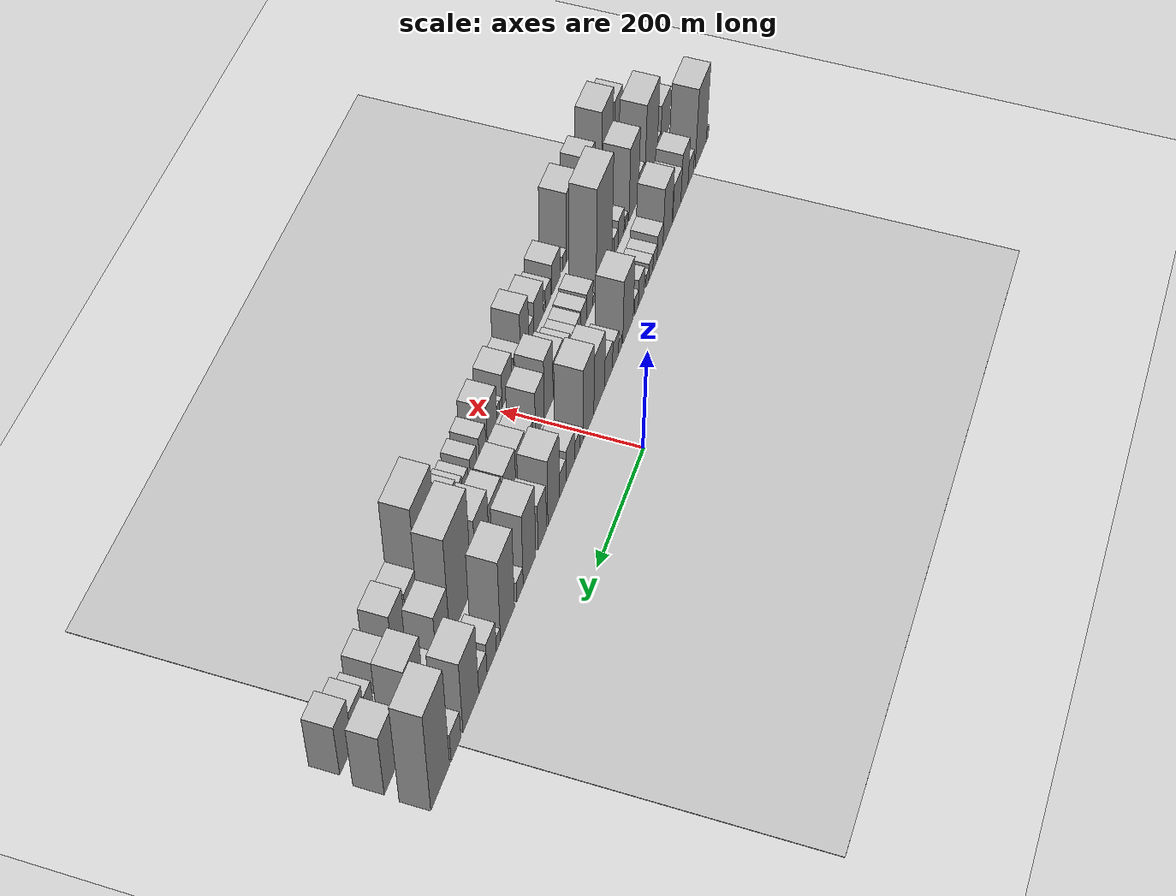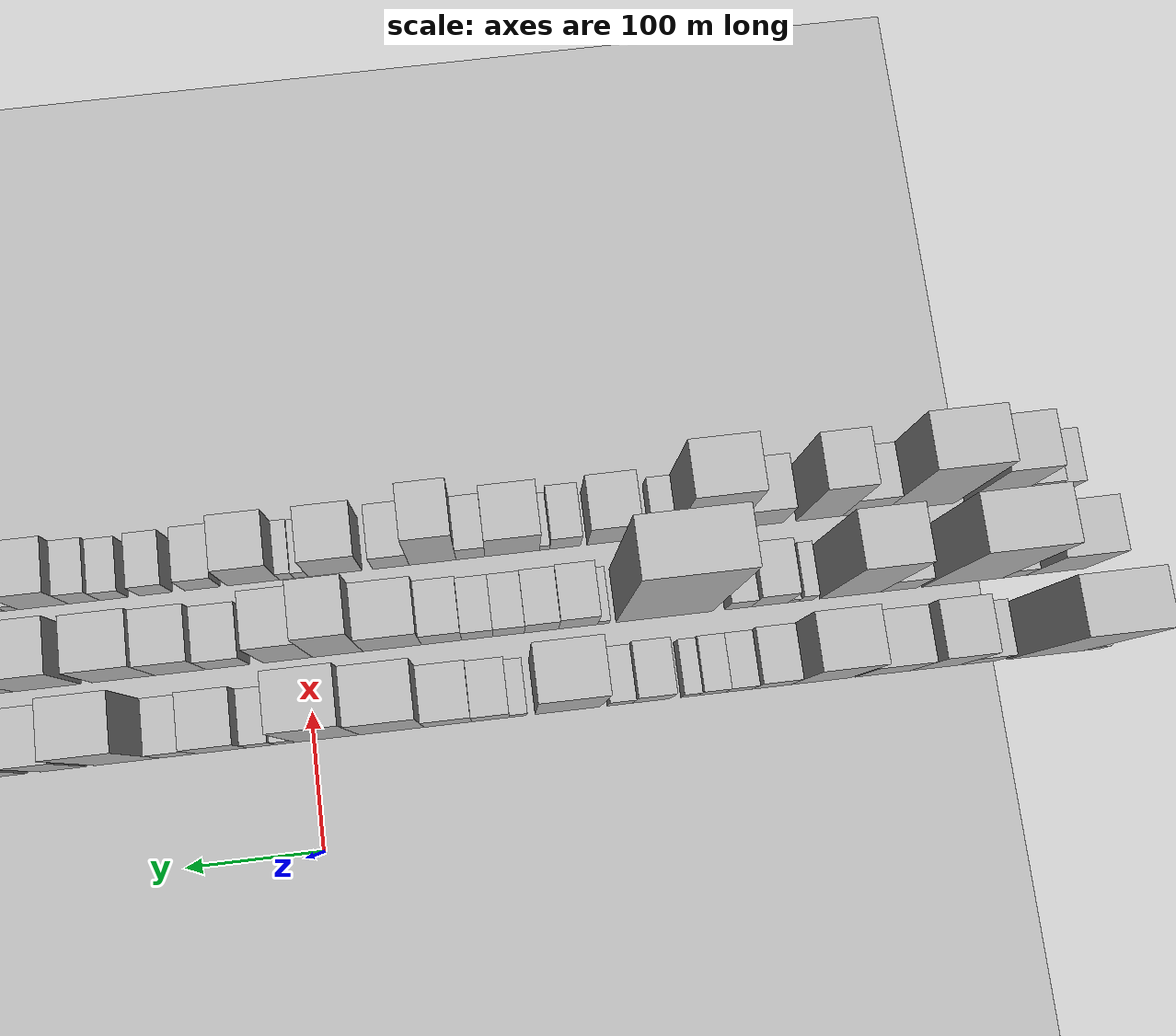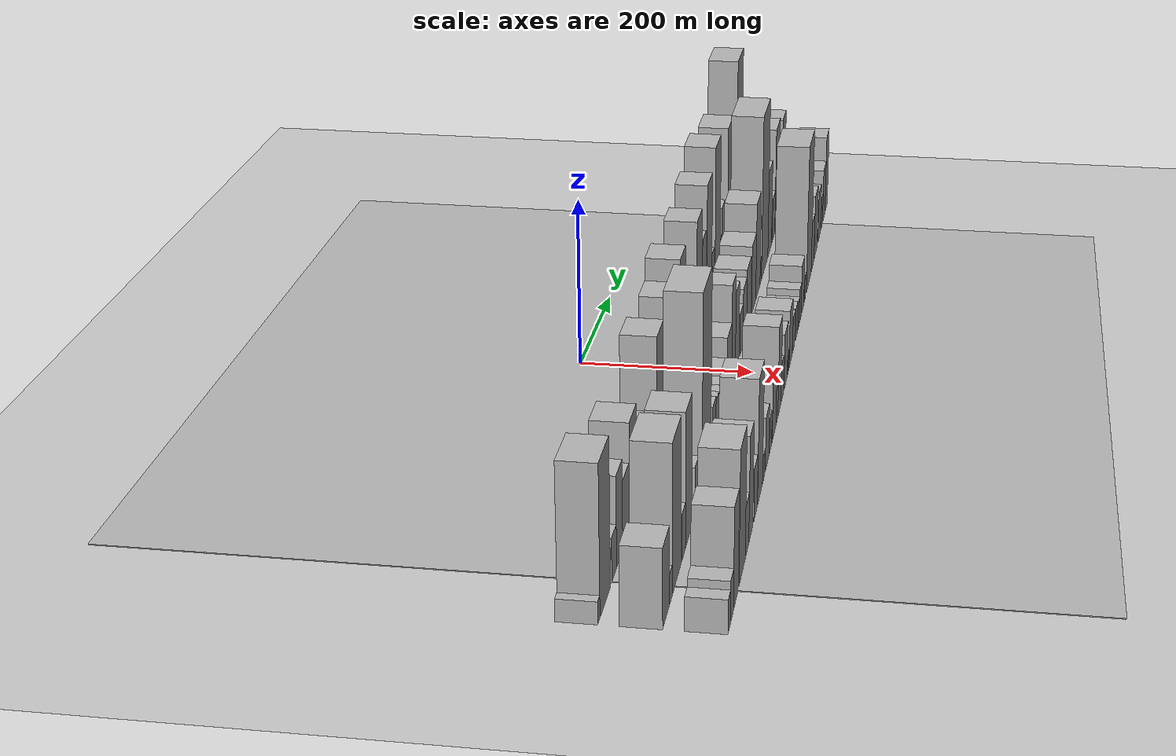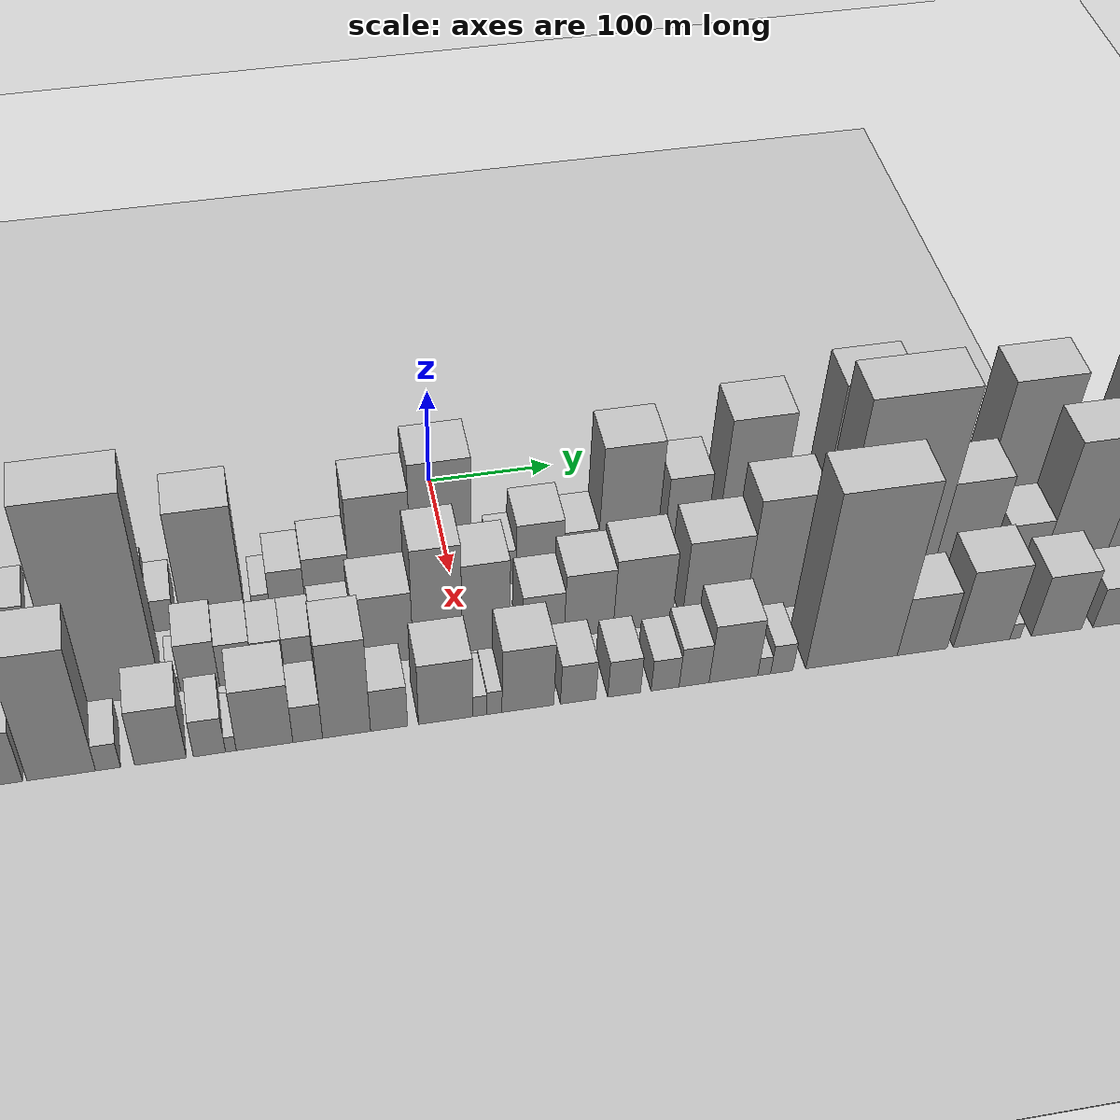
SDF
<?xml version="1.0" encoding="utf-8"?>

<sdf version="1.6">

   <world name="default">

      <gui fullscreen="0">

         <camera name="user_camera">

            <pose>-15 0 4.57585 0 0 0</pose>

            <view_controller>orbit</view_controller>

         </camera>

      </gui>

      <scene>

         <sky>

           <clouds>

             <speed>12</speed>

           </clouds>

         </sky>

         <ambient>0.4 0.4 0.4 1</ambient>

         <background>0.7 0.7 0.7 1</background>

         <shadows>1</shadows>

      </scene>

      <gravity>0 0 -9.8066</gravity>

      <magnetic_field>6e-06 2.3e-05 -4.2e-05</magnetic_field>

      <physics default="0" name="default_physics" type="ode">

         <ode>

            <solver>

               <type>quick</type>

               <iters>10</iters>

               <sor>1.0</sor>

               <use_dynamic_moi_rescaling>0</use_dynamic_moi_rescaling>

            </solver>

            <constraints>

               <cfm>0</cfm>

               <erp>0.2</erp>

               <contact_max_correcting_vel>100</contact_max_correcting_vel>

               <contact_surface_layer>0.001</contact_surface_layer>

            </constraints>

         </ode>

         <max_step_size>0.004</max_step_size>

         <real_time_factor>1</real_time_factor>

         <real_time_update_rate>250</real_time_update_rate>

      </physics>

      <light name="sun" type="directional">

         <cast_shadows>1</cast_shadows>

         <pose>0 0 10 0 0 0</pose>

         <diffuse>0.8 0.8 0.8 1</diffuse>

         <specular>0.2 0.2 0.2 1</specular>

         <attenuation>

            <range>1000</range>

            <constant>0.9</constant>

            <linear>0.01</linear>

            <quadratic>0.001</quadratic>

         </attenuation>

         <direction>-0.5 0.1 -0.9</direction>

      </light>

      <include>

         <name>ground_plane_1</name>

         <uri>model://HANNAS_ground_plane</uri>

         <pose>0 0 0  0 0 0</pose>

      </include>

      <include>

         <name>ground_plane_2</name>

         <uri>model://HANNAS_ground_plane</uri>

         <pose>100 0 0  0 0 0</pose>

      </include>

      <model name="building_1">

         <static>1</static>

         <pose frame="">100.0000 -574.0977 0 0.000000 0.000000 0.000000</pose>

         <link name="link">

            <pose frame="">0 0 12.00 0 0 0</pose>

            <collision name="collision">

               <geometry>

                  <box>

                     <size>40.0000 11.8045 24.0000</size>

                  </box>

               </geometry>

               <max_contacts>10</max_contacts>

               <surface>

                  <contact>

                     <ode/>

                  </contact>

                  <bounce/>

                  <friction>

                     <torsional>

                        <ode/>

                     </torsional>

                     <ode/>

                  </friction>

               </surface>

            </collision>

            <visual name="visual">

               <cast_shadows>0</cast_shadows>

               <geometry>

                  <box>

                     <size>40.0000 11.8045 24.0000</size>

                  </box>

               </geometry>

               <material>

                  <script>

                     <uri>model://HANNAS_wall/materials/scripts</uri>

                     <uri>model://HANNAS_wall/materials/textures</uri>

                     <name>vrc/HANNAS_wall</name>

                  </script>

               </material>

            </visual>

            <self_collide>0</self_collide>

            <enable_wind>0</enable_wind>

            <kinematic>0</kinematic>

         </link>

      </model>

      <model name="building_2">

         <static>1</static>

         <pose frame="">100.0000 -539.3226 0 0.000000 0.000000 0.000000</pose>

         <link name="link">

            <pose frame="">0 0 79.50 0 0 0</pose>

            <collision name="collision">

               <geometry>

                  <box>

                     <size>40.0000 57.7458 159.0000</size>

                  </box>

               </geometry>

               <max_contacts>10</max_contacts>

               <surface>

                  <contact>

                     <ode/>

                  </contact>

                  <bounce/>

                  <friction>

                     <torsional>

                        <ode/>

                     </torsional>

                     <ode/>

                  </friction>

               </surface>

            </collision>

            <visual name="visual">

               <cast_shadows>0</cast_shadows>

               <geometry>

                  <box>

                     <size>40.0000 57.7458 159.0000</size>

                  </box>

               </geometry>

               <material>

                  <script>

                     <uri>model://HANNAS_wall/materials/scripts</uri>

                     <uri>model://HANNAS_wall/materials/textures</uri>

                     <name>vrc/HANNAS_wall</name>

                  </script>

               </material>

            </visual>

            <self_collide>0</self_collide>

            <enable_wind>0</enable_wind>

            <kinematic>0</kinematic>

         </link>

      </model>

      <model name="building_3">

         <static>1</static>

         <pose frame="">100.0000 -488.3909 0 0.000000 0.000000 0.000000</pose>

         <link name="link">

            <pose frame="">0 0 24.00 0 0 0</pose>

            <collision name="collision">

               <geometry>

                  <box>

                     <size>40.0000 28.1177 48.0000</size>

                  </box>

               </geometry>

               <max_contacts>10</max_contacts>

               <surface>

                  <contact>

                     <ode/>

                  </contact>

                  <bounce/>

                  <friction>

                     <torsional>

                        <ode/>

                     </torsional>

                     <ode/>

                  </friction>

               </surface>

            </collision>

            <visual name="visual">

               <cast_shadows>0</cast_shadows>

               <geometry>

                  <box>

                     <size>40.0000 28.1177 48.0000</size>

                  </box>

               </geometry>

               <material>

                  <script>

                     <uri>model://HANNAS_wall/materials/scripts</uri>

                     <uri>model://HANNAS_wall/materials/textures</uri>

                     <name>vrc/HANNAS_wall</name>

                  </script>

               </material>

            </visual>

            <self_collide>0</self_collide>

            <enable_wind>0</enable_wind>

            <kinematic>0</kinematic>

         </link>

      </model>

      <model name="building_4">

         <static>1</static>

         <pose frame="">100.0000 -456.1333 0 0.000000 0.000000 0.000000</pose>

         <link name="link">

            <pose frame="">0 0 49.50 0 0 0</pose>

            <collision name="collision">

               <geometry>

                  <box>

                     <size>40.0000 36.3975 99.0000</size>

                  </box>

               </geometry>

               <max_contacts>10</max_contacts>

               <surface>

                  <contact>

                     <ode/>

                  </contact>

                  <bounce/>

                  <friction>

                     <torsional>

                        <ode/>

                     </torsional>

                     <ode/>

                  </friction>

               </surface>

            </collision>

            <visual name="visual">

               <cast_shadows>0</cast_shadows>

               <geometry>

                  <box>

                     <size>40.0000 36.3975 99.0000</size>

                  </box>

               </geometry>

               <material>

                  <script>

                     <uri>model://HANNAS_wall/materials/scripts</uri>

                     <uri>model://HANNAS_wall/materials/textures</uri>

                     <name>vrc/HANNAS_wall</name>

                  </script>

               </material>

            </visual>

            <self_collide>0</self_collide>

            <enable_wind>0</enable_wind>

            <kinematic>0</kinematic>

         </link>

      </model>

      <model name="building_5">

         <static>1</static>

         <pose frame="">100.0000 -417.6752 0 0.000000 0.000000 0.000000</pose>

         <link name="link">

            <pose frame="">0 0 37.50 0 0 0</pose>

            <collision name="collision">

               <geometry>

                  <box>

                     <size>40.0000 40.5187 75.0000</size>

                  </box>

               </geometry>

               <max_contacts>10</max_contacts>

               <surface>

                  <contact>

                     <ode/>

                  </contact>

                  <bounce/>

                  <friction>

                     <torsional>

                        <ode/>

                     </torsional>

                     <ode/>

                  </friction>

               </surface>

            </collision>

            <visual name="visual">

               <cast_shadows>0</cast_shadows>

               <geometry>

                  <box>

                     <size>40.0000 40.5187 75.0000</size>

                  </box>

               </geometry>

               <material>

                  <script>

                     <uri>model://HANNAS_wall/materials/scripts</uri>

                     <uri>model://HANNAS_wall/materials/textures</uri>

                     <name>vrc/HANNAS_wall</name>

                  </script>

               </material>

            </visual>

            <self_collide>0</self_collide>

            <enable_wind>0</enable_wind>

            <kinematic>0</kinematic>

         </link>

      </model>

      <model name="building_6">

         <static>1</static>

         <pose frame="">100.0000 -372.1113 0 0.000000 0.000000 0.000000</pose>

         <link name="link">

            <pose frame="">0 0 58.50 0 0 0</pose>

            <collision name="collision">

               <geometry>

                  <box>

                     <size>40.0000 44.6091 117.0000</size>

                  </box>

               </geometry>

               <max_contacts>10</max_contacts>

               <surface>

                  <contact>

                     <ode/>

                  </contact>

                  <bounce/>

                  <friction>

                     <torsional>

                        <ode/>

                     </torsional>

                     <ode/>

                  </friction>

               </surface>

            </collision>

            <visual name="visual">

               <cast_shadows>0</cast_shadows>

               <geometry>

                  <box>

                     <size>40.0000 44.6091 117.0000</size>

                  </box>

               </geometry>

               <material>

                  <script>

                     <uri>model://HANNAS_wall/materials/scripts</uri>

                     <uri>model://HANNAS_wall/materials/textures</uri>

                     <name>vrc/HANNAS_wall</name>

                  </script>

               </material>

            </visual>

            <self_collide>0</self_collide>

            <enable_wind>0</enable_wind>

            <kinematic>0</kinematic>

         </link>

      </model>

      <model name="building_7">

         <static>1</static>

         <pose frame="">100.0000 -335.6310 0 0.000000 0.000000 0.000000</pose>

         <link name="link">

            <pose frame="">0 0 25.50 0 0 0</pose>

            <collision name="collision">

               <geometry>

                  <box>

                     <size>40.0000 28.3515 51.0000</size>

                  </box>

               </geometry>

               <max_contacts>10</max_contacts>

               <surface>

                  <contact>

                     <ode/>

                  </contact>

                  <bounce/>

                  <friction>

                     <torsional>

                        <ode/>

                     </torsional>

                     <ode/>

                  </friction>

               </surface>

            </collision>

            <visual name="visual">

               <cast_shadows>0</cast_shadows>

               <geometry>

                  <box>

                     <size>40.0000 28.3515 51.0000</size>

                  </box>

               </geometry>

               <material>

                  <script>

                     <uri>model://HANNAS_wall/materials/scripts</uri>

                     <uri>model://HANNAS_wall/materials/textures</uri>

                     <name>vrc/HANNAS_wall</name>

                  </script>

               </material>

            </visual>

            <self_collide>0</self_collide>

            <enable_wind>0</enable_wind>

            <kinematic>0</kinematic>

         </link>

      </model>

      <model name="building_8">

         <static>1</static>

         <pose frame="">100.0000 -311.3759 0 0.000000 0.000000 0.000000</pose>

         <link name="link">

            <pose frame="">0 0 18.00 0 0 0</pose>

            <collision name="collision">

               <geometry>

                  <box>

                     <size>40.0000 20.1587 36.0000</size>

                  </box>

               </geometry>

               <max_contacts>10</max_contacts>

               <surface>

                  <contact>

                     <ode/>

                  </contact>

                  <bounce/>

                  <friction>

                     <torsional>

                        <ode/>

                     </torsional>

                     <ode/>

                  </friction>

               </surface>

            </collision>

            <visual name="visual">

               <cast_shadows>0</cast_shadows>

               <geometry>

                  <box>

                     <size>40.0000 20.1587 36.0000</size>

                  </box>

               </geometry>

               <material>

                  <script>

                     <uri>model://HANNAS_wall/materials/scripts</uri>

                     <uri>model://HANNAS_wall/materials/textures</uri>

                     <name>vrc/HANNAS_wall</name>

                  </script>

               </material>

            </visual>

            <self_collide>0</self_collide>

            <enable_wind>0</enable_wind>

            <kinematic>0</kinematic>

         </link>

      </model>

      <model name="building_9">

         <static>1</static>

         <pose frame="">100.0000 -291.4509 0 0.000000 0.000000 0.000000</pose>

         <link name="link">

            <pose frame="">0 0 18.00 0 0 0</pose>

            <collision name="collision">

               <geometry>

                  <box>

                     <size>40.0000 19.6914 36.0000</size>

                  </box>

               </geometry>

               <max_contacts>10</max_contacts>

               <surface>

                  <contact>

                     <ode/>

                  </contact>

                  <bounce/>

                  <friction>

                     <torsional>

                        <ode/>

                     </torsional>

                     <ode/>

                  </friction>

               </surface>

            </collision>

            <visual name="visual">

               <cast_shadows>0</cast_shadows>

               <geometry>

                  <box>

                     <size>40.0000 19.6914 36.0000</size>

                  </box>

               </geometry>

               <material>

                  <script>

                     <uri>model://HANNAS_wall/materials/scripts</uri>

                     <uri>model://HANNAS_wall/materials/textures</uri>

                     <name>vrc/HANNAS_wall</name>

                  </script>

               </material>

            </visual>

            <self_collide>0</self_collide>

            <enable_wind>0</enable_wind>

            <kinematic>0</kinematic>

         </link>

      </model>

      <model name="building_10">

         <static>1</static>

         <pose frame="">100.0000 -275.0171 0 0.000000 0.000000 0.000000</pose>

         <link name="link">

            <pose frame="">0 0 13.50 0 0 0</pose>

            <collision name="collision">

               <geometry>

                  <box>

                     <size>40.0000 13.1762 27.0000</size>

                  </box>

               </geometry>

               <max_contacts>10</max_contacts>

               <surface>

                  <contact>

                     <ode/>

                  </contact>

                  <bounce/>

                  <friction>

                     <torsional>

                        <ode/>

                     </torsional>

                     <ode/>

                  </friction>

               </surface>

            </collision>

            <visual name="visual">

               <cast_shadows>0</cast_shadows>

               <geometry>

                  <box>

                     <size>40.0000 13.1762 27.0000</size>

                  </box>

               </geometry>

               <material>

                  <script>

                     <uri>model://HANNAS_wall/materials/scripts</uri>

                     <uri>model://HANNAS_wall/materials/textures</uri>

                     <name>vrc/HANNAS_wall</name>

                  </script>

               </material>

            </visual>

            <self_collide>0</self_collide>

            <enable_wind>0</enable_wind>

            <kinematic>0</kinematic>

         </link>

      </model>

      <model name="building_11">

         <static>1</static>

         <pose frame="">100.0000 -246.7445 0 0.000000 0.000000 0.000000</pose>

         <link name="link">

            <pose frame="">0 0 27.00 0 0 0</pose>

            <collision name="collision">

               <geometry>

                  <box>

                     <size>40.0000 27.3691 54.0000</size>

                  </box>

               </geometry>

               <max_contacts>10</max_contacts>

               <surface>

                  <contact>

                     <ode/>

                  </contact>

                  <bounce/>

                  <friction>

                     <torsional>

                        <ode/>

                     </torsional>

                     <ode/>

                  </friction>

               </surface>

            </collision>

            <visual name="visual">

               <cast_shadows>0</cast_shadows>

               <geometry>

                  <box>

                     <size>40.0000 27.3691 54.0000</size>

                  </box>

               </geometry>

               <material>

                  <script>

                     <uri>model://HANNAS_wall/materials/scripts</uri>

                     <uri>model://HANNAS_wall/materials/textures</uri>

                     <name>vrc/HANNAS_wall</name>

                  </script>

               </material>

            </visual>

            <self_collide>0</self_collide>

            <enable_wind>0</enable_wind>

            <kinematic>0</kinematic>

         </link>

      </model>

      <model name="building_12">

         <static>1</static>

         <pose frame="">100.0000 -223.6213 0 0.000000 0.000000 0.000000</pose>

         <link name="link">

            <pose frame="">0 0 18.00 0 0 0</pose>

            <collision name="collision">

               <geometry>

                  <box>

                     <size>40.0000 18.8772 36.0000</size>

                  </box>

               </geometry>

               <max_contacts>10</max_contacts>

               <surface>

                  <contact>

                     <ode/>

                  </contact>

                  <bounce/>

                  <friction>

                     <torsional>

                        <ode/>

                     </torsional>

                     <ode/>

                  </friction>

               </surface>

            </collision>

            <visual name="visual">

               <cast_shadows>0</cast_shadows>

               <geometry>

                  <box>

                     <size>40.0000 18.8772 36.0000</size>

                  </box>

               </geometry>

               <material>

                  <script>

                     <uri>model://HANNAS_wall/materials/scripts</uri>

                     <uri>model://HANNAS_wall/materials/textures</uri>

                     <name>vrc/HANNAS_wall</name>

                  </script>

               </material>

            </visual>

            <self_collide>0</self_collide>

            <enable_wind>0</enable_wind>

            <kinematic>0</kinematic>

         </link>

      </model>

      <model name="building_13">

         <static>1</static>

         <pose frame="">100.0000 -185.1757 0 0.000000 0.000000 0.000000</pose>

         <link name="link">

            <pose frame="">0 0 64.50 0 0 0</pose>

            <collision name="collision">

               <geometry>

                  <box>

                     <size>40.0000 48.0139 129.0000</size>

                  </box>

               </geometry>

               <max_contacts>10</max_contacts>

               <surface>

                  <contact>

                     <ode/>

                  </contact>

                  <bounce/>

                  <friction>

                     <torsional>

                        <ode/>

                     </torsional>

                     <ode/>

                  </friction>

               </surface>

            </collision>

            <visual name="visual">

               <cast_shadows>0</cast_shadows>

               <geometry>

                  <box>

                     <size>40.0000 48.0139 129.0000</size>

                  </box>

               </geometry>

               <material>

                  <script>

                     <uri>model://HANNAS_wall/materials/scripts</uri>

                     <uri>model://HANNAS_wall/materials/textures</uri>

                     <name>vrc/HANNAS_wall</name>

                  </script>

               </material>

            </visual>

            <self_collide>0</self_collide>

            <enable_wind>0</enable_wind>

            <kinematic>0</kinematic>

         </link>

      </model>

      <model name="building_14">

         <static>1</static>

         <pose frame="">100.0000 -148.5750 0 0.000000 0.000000 0.000000</pose>

         <link name="link">

            <pose frame="">0 0 13.50 0 0 0</pose>

            <collision name="collision">

               <geometry>

                  <box>

                     <size>40.0000 13.1874 27.0000</size>

                  </box>

               </geometry>

               <max_contacts>10</max_contacts>

               <surface>

                  <contact>

                     <ode/>

                  </contact>

                  <bounce/>

                  <friction>

                     <torsional>

                        <ode/>

                     </torsional>

                     <ode/>

                  </friction>

               </surface>

            </collision>

            <visual name="visual">

               <cast_shadows>0</cast_shadows>

               <geometry>

                  <box>

                     <size>40.0000 13.1874 27.0000</size>

                  </box>

               </geometry>

               <material>

                  <script>

                     <uri>model://HANNAS_wall/materials/scripts</uri>

                     <uri>model://HANNAS_wall/materials/textures</uri>

                     <name>vrc/HANNAS_wall</name>

                  </script>

               </material>

            </visual>

            <self_collide>0</self_collide>

            <enable_wind>0</enable_wind>

            <kinematic>0</kinematic>

         </link>

      </model>

      <model name="building_15">

         <static>1</static>

         <pose frame="">100.0000 -128.4397 0 0.000000 0.000000 0.000000</pose>

         <link name="link">

            <pose frame="">0 0 25.50 0 0 0</pose>

            <collision name="collision">

               <geometry>

                  <box>

                     <size>40.0000 27.0833 51.0000</size>

                  </box>

               </geometry>

               <max_contacts>10</max_contacts>

               <surface>

                  <contact>

                     <ode/>

                  </contact>

                  <bounce/>

                  <friction>

                     <torsional>

                        <ode/>

                     </torsional>

                     <ode/>

                  </friction>

               </surface>

            </collision>

            <visual name="visual">

               <cast_shadows>0</cast_shadows>

               <geometry>

                  <box>

                     <size>40.0000 27.0833 51.0000</size>

                  </box>

               </geometry>

               <material>

                  <script>

                     <uri>model://HANNAS_wall/materials/scripts</uri>

                     <uri>model://HANNAS_wall/materials/textures</uri>

                     <name>vrc/HANNAS_wall</name>

                  </script>

               </material>

            </visual>

            <self_collide>0</self_collide>

            <enable_wind>0</enable_wind>

            <kinematic>0</kinematic>

         </link>

      </model>

      <model name="building_16">

         <static>1</static>

         <pose frame="">100.0000 -97.4755 0 0.000000 0.000000 0.000000</pose>

         <link name="link">

            <pose frame="">0 0 30.00 0 0 0</pose>

            <collision name="collision">

               <geometry>

                  <box>

                     <size>40.0000 34.8450 60.0000</size>

                  </box>

               </geometry>

               <max_contacts>10</max_contacts>

               <surface>

                  <contact>

                     <ode/>

                  </contact>

                  <bounce/>

                  <friction>

                     <torsional>

                        <ode/>

                     </torsional>

                     <ode/>

                  </friction>

               </surface>

            </collision>

            <visual name="visual">

               <cast_shadows>0</cast_shadows>

               <geometry>

                  <box>

                     <size>40.0000 34.8450 60.0000</size>

                  </box>

               </geometry>

               <material>

                  <script>

                     <uri>model://HANNAS_wall/materials/scripts</uri>

                     <uri>model://HANNAS_wall/materials/textures</uri>

                     <name>vrc/HANNAS_wall</name>

                  </script>

               </material>

            </visual>

            <self_collide>0</self_collide>

            <enable_wind>0</enable_wind>

            <kinematic>0</kinematic>

         </link>

      </model>

      <model name="building_17">

         <static>1</static>

         <pose frame="">100.0000 -56.4032 0 0.000000 0.000000 0.000000</pose>

         <link name="link">

            <pose frame="">0 0 60.00 0 0 0</pose>

            <collision name="collision">

               <geometry>

                  <box>

                     <size>40.0000 47.2996 120.0000</size>

                  </box>

               </geometry>

               <max_contacts>10</max_contacts>

               <surface>

                  <contact>

                     <ode/>

                  </contact>

                  <bounce/>

                  <friction>

                     <torsional>

                        <ode/>

                     </torsional>

                     <ode/>

                  </friction>

               </surface>

            </collision>

            <visual name="visual">

               <cast_shadows>0</cast_shadows>

               <geometry>

                  <box>

                     <size>40.0000 47.2996 120.0000</size>

                  </box>

               </geometry>

               <material>

                  <script>

                     <uri>model://HANNAS_wall/materials/scripts</uri>

                     <uri>model://HANNAS_wall/materials/textures</uri>

                     <name>vrc/HANNAS_wall</name>

                  </script>

               </material>

            </visual>

            <self_collide>0</self_collide>

            <enable_wind>0</enable_wind>

            <kinematic>0</kinematic>

         </link>

      </model>

      <model name="building_18">

         <static>1</static>

         <pose frame="">100.0000 -9.4550 0 0.000000 0.000000 0.000000</pose>

         <link name="link">

            <pose frame="">0 0 73.50 0 0 0</pose>

            <collision name="collision">

               <geometry>

                  <box>

                     <size>40.0000 46.5969 147.0000</size>

                  </box>

               </geometry>

               <max_contacts>10</max_contacts>

               <surface>

                  <contact>

                     <ode/>

                  </contact>

                  <bounce/>

                  <friction>

                     <torsional>

                        <ode/>

                     </torsional>

                     <ode/>

                  </friction>

               </surface>

            </collision>

            <visual name="visual">

               <cast_shadows>0</cast_shadows>

               <geometry>

                  <box>

                     <size>40.0000 46.5969 147.0000</size>

                  </box>

               </geometry>

               <material>

                  <script>

                     <uri>model://HANNAS_wall/materials/scripts</uri>

                     <uri>model://HANNAS_wall/materials/textures</uri>

                     <name>vrc/HANNAS_wall</name>

                  </script>

               </material>

            </visual>

            <self_collide>0</self_collide>

            <enable_wind>0</enable_wind>

            <kinematic>0</kinematic>

         </link>

      </model>

      <model name="building_19">

         <static>1</static>

         <pose frame="">100.0000 21.3931 0 0.000000 0.000000 0.000000</pose>

         <link name="link">

            <pose frame="">0 0 15.00 0 0 0</pose>

            <collision name="collision">

               <geometry>

                  <box>

                     <size>40.0000 15.0992 30.0000</size>

                  </box>

               </geometry>

               <max_contacts>10</max_contacts>

               <surface>

                  <contact>

                     <ode/>

                  </contact>

                  <bounce/>

                  <friction>

                     <torsional>

                        <ode/>

                     </torsional>

                     <ode/>

                  </friction>

               </surface>

            </collision>

            <visual name="visual">

               <cast_shadows>0</cast_shadows>

               <geometry>

                  <box>

                     <size>40.0000 15.0992 30.0000</size>

                  </box>

               </geometry>

               <material>

                  <script>

                     <uri>model://HANNAS_wall/materials/scripts</uri>

                     <uri>model://HANNAS_wall/materials/textures</uri>

                     <name>vrc/HANNAS_wall</name>

                  </script>

               </material>

            </visual>

            <self_collide>0</self_collide>

            <enable_wind>0</enable_wind>

            <kinematic>0</kinematic>

         </link>

      </model>

      <model name="building_20">

         <static>1</static>

         <pose frame="">100.0000 38.8198 0 0.000000 0.000000 0.000000</pose>

         <link name="link">

            <pose frame="">0 0 19.50 0 0 0</pose>

            <collision name="collision">

               <geometry>

                  <box>

                     <size>40.0000 19.7542 39.0000</size>

                  </box>

               </geometry>

               <max_contacts>10</max_contacts>

               <surface>

                  <contact>

                     <ode/>

                  </contact>

                  <bounce/>

                  <friction>

                     <torsional>

                        <ode/>

                     </torsional>

                     <ode/>

                  </friction>

               </surface>

            </collision>

            <visual name="visual">

               <cast_shadows>0</cast_shadows>

               <geometry>

                  <box>

                     <size>40.0000 19.7542 39.0000</size>

                  </box>

               </geometry>

               <material>

                  <script>

                     <uri>model://HANNAS_wall/materials/scripts</uri>

                     <uri>model://HANNAS_wall/materials/textures</uri>

                     <name>vrc/HANNAS_wall</name>

                  </script>

               </material>

            </visual>

            <self_collide>0</self_collide>

            <enable_wind>0</enable_wind>

            <kinematic>0</kinematic>

         </link>

      </model>

      <model name="building_21">

         <static>1</static>

         <pose frame="">100.0000 67.3922 0 0.000000 0.000000 0.000000</pose>

         <link name="link">

            <pose frame="">0 0 33.00 0 0 0</pose>

            <collision name="collision">

               <geometry>

                  <box>

                     <size>40.0000 37.3905 66.0000</size>

                  </box>

               </geometry>

               <max_contacts>10</max_contacts>

               <surface>

                  <contact>

                     <ode/>

                  </contact>

                  <bounce/>

                  <friction>

                     <torsional>

                        <ode/>

                     </torsional>

                     <ode/>

                  </friction>

               </surface>

            </collision>

            <visual name="visual">

               <cast_shadows>0</cast_shadows>

               <geometry>

                  <box>

                     <size>40.0000 37.3905 66.0000</size>

                  </box>

               </geometry>

               <material>

                  <script>

                     <uri>model://HANNAS_wall/materials/scripts</uri>

                     <uri>model://HANNAS_wall/materials/textures</uri>

                     <name>vrc/HANNAS_wall</name>

                  </script>

               </material>

            </visual>

            <self_collide>0</self_collide>

            <enable_wind>0</enable_wind>

            <kinematic>0</kinematic>

         </link>

      </model>

      <model name="building_22">

         <static>1</static>

         <pose frame="">100.0000 99.5906 0 0.000000 0.000000 0.000000</pose>

         <link name="link">

            <pose frame="">0 0 25.50 0 0 0</pose>

            <collision name="collision">

               <geometry>

                  <box>

                     <size>40.0000 27.0063 51.0000</size>

                  </box>

               </geometry>

               <max_contacts>10</max_contacts>

               <surface>

                  <contact>

                     <ode/>

                  </contact>

                  <bounce/>

                  <friction>

                     <torsional>

                        <ode/>

                     </torsional>

                     <ode/>

                  </friction>

               </surface>

            </collision>

            <visual name="visual">

               <cast_shadows>0</cast_shadows>

               <geometry>

                  <box>

                     <size>40.0000 27.0063 51.0000</size>

                  </box>

               </geometry>

               <material>

                  <script>

                     <uri>model://HANNAS_wall/materials/scripts</uri>

                     <uri>model://HANNAS_wall/materials/textures</uri>

                     <name>vrc/HANNAS_wall</name>

                  </script>

               </material>

            </visual>

            <self_collide>0</self_collide>

            <enable_wind>0</enable_wind>

            <kinematic>0</kinematic>

         </link>

      </model>

      <model name="building_23">

         <static>1</static>

         <pose frame="">100.0000 136.3201 0 0.000000 0.000000 0.000000</pose>

         <link name="link">

            <pose frame="">0 0 69.00 0 0 0</pose>

            <collision name="collision">

               <geometry>

                  <box>

                     <size>40.0000 46.4527 138.0000</size>

                  </box>

               </geometry>

               <max_contacts>10</max_contacts>

               <surface>

                  <contact>

                     <ode/>

                  </contact>

                  <bounce/>

                  <friction>

                     <torsional>

                        <ode/>

                     </torsional>

                     <ode/>

                  </friction>

               </surface>

            </collision>

            <visual name="visual">

               <cast_shadows>0</cast_shadows>

               <geometry>

                  <box>

                     <size>40.0000 46.4527 138.0000</size>

                  </box>

               </geometry>

               <material>

                  <script>

                     <uri>model://HANNAS_wall/materials/scripts</uri>

                     <uri>model://HANNAS_wall/materials/textures</uri>

                     <name>vrc/HANNAS_wall</name>

                  </script>

               </material>

            </visual>

            <self_collide>0</self_collide>

            <enable_wind>0</enable_wind>

            <kinematic>0</kinematic>

         </link>

      </model>

      <model name="building_24">

         <static>1</static>

         <pose frame="">100.0000 182.3514 0 0.000000 0.000000 0.000000</pose>

         <link name="link">

            <pose frame="">0 0 48.00 0 0 0</pose>

            <collision name="collision">

               <geometry>

                  <box>

                     <size>40.0000 33.6099 96.0000</size>

                  </box>

               </geometry>

               <max_contacts>10</max_contacts>

               <surface>

                  <contact>

                     <ode/>

                  </contact>

                  <bounce/>

                  <friction>

                     <torsional>

                        <ode/>

                     </torsional>

                     <ode/>

                  </friction>

               </surface>

            </collision>

            <visual name="visual">

               <cast_shadows>0</cast_shadows>

               <geometry>

                  <box>

                     <size>40.0000 33.6099 96.0000</size>

                  </box>

               </geometry>

               <material>

                  <script>

                     <uri>model://HANNAS_wall/materials/scripts</uri>

                     <uri>model://HANNAS_wall/materials/textures</uri>

                     <name>vrc/HANNAS_wall</name>

                  </script>

               </material>

            </visual>

            <self_collide>0</self_collide>

            <enable_wind>0</enable_wind>

            <kinematic>0</kinematic>

         </link>

      </model>

      <model name="building_25">

         <static>1</static>

         <pose frame="">100.0000 232.7722 0 0.000000 0.000000 0.000000</pose>

         <link name="link">

            <pose frame="">0 0 75.00 0 0 0</pose>

            <collision name="collision">

               <geometry>

                  <box>

                     <size>40.0000 49.2317 150.0000</size>

                  </box>

               </geometry>

               <max_contacts>10</max_contacts>

               <surface>

                  <contact>

                     <ode/>

                  </contact>

                  <bounce/>

                  <friction>

                     <torsional>

                        <ode/>

                     </torsional>

                     <ode/>

                  </friction>

               </surface>

            </collision>

            <visual name="visual">

               <cast_shadows>0</cast_shadows>

               <geometry>

                  <box>

                     <size>40.0000 49.2317 150.0000</size>

                  </box>

               </geometry>

               <material>

                  <script>

                     <uri>model://HANNAS_wall/materials/scripts</uri>

                     <uri>model://HANNAS_wall/materials/textures</uri>

                     <name>vrc/HANNAS_wall</name>

                  </script>

               </material>

            </visual>

            <self_collide>0</self_collide>

            <enable_wind>0</enable_wind>

            <kinematic>0</kinematic>

         </link>

      </model>

      <model name="building_26">

         <static>1</static>

         <pose frame="">100.0000 269.8020 0 0.000000 0.000000 0.000000</pose>

         <link name="link">

            <pose frame="">0 0 21.00 0 0 0</pose>

            <collision name="collision">

               <geometry>

                  <box>

                     <size>40.0000 24.8280 42.0000</size>

                  </box>

               </geometry>

               <max_contacts>10</max_contacts>

               <surface>

                  <contact>

                     <ode/>

                  </contact>

                  <bounce/>

                  <friction>

                     <torsional>

                        <ode/>

                     </torsional>

                     <ode/>

                  </friction>

               </surface>

            </collision>

            <visual name="visual">

               <cast_shadows>0</cast_shadows>

               <geometry>

                  <box>

                     <size>40.0000 24.8280 42.0000</size>

                  </box>

               </geometry>

               <material>

                  <script>

                     <uri>model://HANNAS_wall/materials/scripts</uri>

                     <uri>model://HANNAS_wall/materials/textures</uri>

                     <name>vrc/HANNAS_wall</name>

                  </script>

               </material>

            </visual>

            <self_collide>0</self_collide>

            <enable_wind>0</enable_wind>

            <kinematic>0</kinematic>

         </link>

      </model>

      <model name="building_27">

         <static>1</static>

         <pose frame="">100.0000 317.7965 0 0.000000 0.000000 0.000000</pose>

         <link name="link">

            <pose frame="">0 0 85.50 0 0 0</pose>

            <collision name="collision">

               <geometry>

                  <box>

                     <size>40.0000 53.1611 171.0000</size>

                  </box>

               </geometry>

               <max_contacts>10</max_contacts>

               <surface>

                  <contact>

                     <ode/>

                  </contact>

                  <bounce/>

                  <friction>

                     <torsional>

                        <ode/>

                     </torsional>

                     <ode/>

                  </friction>

               </surface>

            </collision>

            <visual name="visual">

               <cast_shadows>0</cast_shadows>

               <geometry>

                  <box>

                     <size>40.0000 53.1611 171.0000</size>

                  </box>

               </geometry>

               <material>

                  <script>

                     <uri>model://HANNAS_wall/materials/scripts</uri>

                     <uri>model://HANNAS_wall/materials/textures</uri>

                     <name>vrc/HANNAS_wall</name>

                  </script>

               </material>

            </visual>

            <self_collide>0</self_collide>

            <enable_wind>0</enable_wind>

            <kinematic>0</kinematic>

         </link>

      </model>

      <model name="building_28">

         <static>1</static>

         <pose frame="">100.0000 352.1460 0 0.000000 0.000000 0.000000</pose>

         <link name="link">

            <pose frame="">0 0 15.00 0 0 0</pose>

            <collision name="collision">

               <geometry>

                  <box>

                     <size>40.0000 15.5379 30.0000</size>

                  </box>

               </geometry>

               <max_contacts>10</max_contacts>

               <surface>

                  <contact>

                     <ode/>

                  </contact>

                  <bounce/>

                  <friction>

                     <torsional>

                        <ode/>

                     </torsional>

                     <ode/>

                  </friction>

               </surface>

            </collision>

            <visual name="visual">

               <cast_shadows>0</cast_shadows>

               <geometry>

                  <box>

                     <size>40.0000 15.5379 30.0000</size>

                  </box>

               </geometry>

               <material>

                  <script>

                     <uri>model://HANNAS_wall/materials/scripts</uri>

                     <uri>model://HANNAS_wall/materials/textures</uri>

                     <name>vrc/HANNAS_wall</name>

                  </script>

               </material>

            </visual>

            <self_collide>0</self_collide>

            <enable_wind>0</enable_wind>

            <kinematic>0</kinematic>

         </link>

      </model>

      <model name="building_29">

         <static>1</static>

         <pose frame="">100.0000 377.1503 0 0.000000 0.000000 0.000000</pose>

         <link name="link">

            <pose frame="">0 0 33.00 0 0 0</pose>

            <collision name="collision">

               <geometry>

                  <box>

                     <size>40.0000 34.4706 66.0000</size>

                  </box>

               </geometry>

               <max_contacts>10</max_contacts>

               <surface>

                  <contact>

                     <ode/>

                  </contact>

                  <bounce/>

                  <friction>

                     <torsional>

                        <ode/>

                     </torsional>

                     <ode/>

                  </friction>

               </surface>

            </collision>

            <visual name="visual">

               <cast_shadows>0</cast_shadows>

               <geometry>

                  <box>

                     <size>40.0000 34.4706 66.0000</size>

                  </box>

               </geometry>

               <material>

                  <script>

                     <uri>model://HANNAS_wall/materials/scripts</uri>

                     <uri>model://HANNAS_wall/materials/textures</uri>

                     <name>vrc/HANNAS_wall</name>

                  </script>

               </material>

            </visual>

            <self_collide>0</self_collide>

            <enable_wind>0</enable_wind>

            <kinematic>0</kinematic>

         </link>

      </model>

      <model name="building_30">

         <static>1</static>

         <pose frame="">100.0000 409.5093 0 0.000000 0.000000 0.000000</pose>

         <link name="link">

            <pose frame="">0 0 25.50 0 0 0</pose>

            <collision name="collision">

               <geometry>

                  <box>

                     <size>40.0000 30.2474 51.0000</size>

                  </box>

               </geometry>

               <max_contacts>10</max_contacts>

               <surface>

                  <contact>

                     <ode/>

                  </contact>

                  <bounce/>

                  <friction>

                     <torsional>

                        <ode/>

                     </torsional>

                     <ode/>

                  </friction>

               </surface>

            </collision>

            <visual name="visual">

               <cast_shadows>0</cast_shadows>

               <geometry>

                  <box>

                     <size>40.0000 30.2474 51.0000</size>

                  </box>

               </geometry>

               <material>

                  <script>

                     <uri>model://HANNAS_wall/materials/scripts</uri>

                     <uri>model://HANNAS_wall/materials/textures</uri>

                     <name>vrc/HANNAS_wall</name>

                  </script>

               </material>

            </visual>

            <self_collide>0</self_collide>

            <enable_wind>0</enable_wind>

            <kinematic>0</kinematic>

         </link>

      </model>

      <model name="building_31">

         <static>1</static>

         <pose frame="">100.0000 453.1934 0 0.000000 0.000000 0.000000</pose>

         <link name="link">

            <pose frame="">0 0 76.50 0 0 0</pose>

            <collision name="collision">

               <geometry>

                  <box>

                     <size>40.0000 57.1208 153.0000</size>

                  </box>

               </geometry>

               <max_contacts>10</max_contacts>

               <surface>

                  <contact>

                     <ode/>

                  </contact>

                  <bounce/>

                  <friction>

                     <torsional>

                        <ode/>

                     </torsional>

                     <ode/>

                  </friction>

               </surface>

            </collision>

            <visual name="visual">

               <cast_shadows>0</cast_shadows>

               <geometry>

                  <box>

                     <size>40.0000 57.1208 153.0000</size>

                  </box>

               </geometry>

               <material>

                  <script>

                     <uri>model://HANNAS_wall/materials/scripts</uri>

                     <uri>model://HANNAS_wall/materials/textures</uri>

                     <name>vrc/HANNAS_wall</name>

                  </script>

               </material>

            </visual>

            <self_collide>0</self_collide>

            <enable_wind>0</enable_wind>

            <kinematic>0</kinematic>

         </link>

      </model>

      <model name="building_32">

         <static>1</static>

         <pose frame="">100.0000 506.1167 0 0.000000 0.000000 0.000000</pose>

         <link name="link">

            <pose frame="">0 0 30.00 0 0 0</pose>

            <collision name="collision">

               <geometry>

                  <box>

                     <size>40.0000 34.7259 60.0000</size>

                  </box>

               </geometry>

               <max_contacts>10</max_contacts>

               <surface>

                  <contact>

                     <ode/>

                  </contact>

                  <bounce/>

                  <friction>

                     <torsional>

                        <ode/>

                     </torsional>

                     <ode/>

                  </friction>

               </surface>

            </collision>

            <visual name="visual">

               <cast_shadows>0</cast_shadows>

               <geometry>

                  <box>

                     <size>40.0000 34.7259 60.0000</size>

                  </box>

               </geometry>

               <material>

                  <script>

                     <uri>model://HANNAS_wall/materials/scripts</uri>

                     <uri>model://HANNAS_wall/materials/textures</uri>

                     <name>vrc/HANNAS_wall</name>

                  </script>

               </material>

            </visual>

            <self_collide>0</self_collide>

            <enable_wind>0</enable_wind>

            <kinematic>0</kinematic>

         </link>

      </model>

      <model name="building_33">

         <static>1</static>

         <pose frame="">100.0000 561.1260 0 0.000000 0.000000 0.000000</pose>

         <link name="link">

            <pose frame="">0 0 106.50 0 0 0</pose>

            <collision name="collision">

               <geometry>

                  <box>

                     <size>40.0000 65.2927 213.0000</size>

                  </box>

               </geometry>

               <max_contacts>10</max_contacts>

               <surface>

                  <contact>

                     <ode/>

                  </contact>

                  <bounce/>

                  <friction>

                     <torsional>

                        <ode/>

                     </torsional>

                     <ode/>

                  </friction>

               </surface>

            </collision>

            <visual name="visual">

               <cast_shadows>0</cast_shadows>

               <geometry>

                  <box>

                     <size>40.0000 65.2927 213.0000</size>

                  </box>

               </geometry>

               <material>

                  <script>

                     <uri>model://HANNAS_wall/materials/scripts</uri>

                     <uri>model://HANNAS_wall/materials/textures</uri>

                     <name>vrc/HANNAS_wall</name>

                  </script>

               </material>

            </visual>

            <self_collide>0</self_collide>

            <enable_wind>0</enable_wind>

            <kinematic>0</kinematic>

         </link>

      </model>

      <model name="building_34">

         <static>1</static>

         <pose frame="">160.0000 -557.8191 0 0.000000 0.000000 0.000000</pose>

         <link name="link">

            <pose frame="">0 0 42.00 0 0 0</pose>

            <collision name="collision">

               <geometry>

                  <box>

                     <size>40.0000 44.3619 84.0000</size>

                  </box>

               </geometry>

               <max_contacts>10</max_contacts>

               <surface>

                  <contact>

                     <ode/>

                  </contact>

                  <bounce/>

                  <friction>

                     <torsional>

                        <ode/>

                     </torsional>

                     <ode/>

                  </friction>

               </surface>

            </collision>

            <visual name="visual">

               <cast_shadows>0</cast_shadows>

               <geometry>

                  <box>

                     <size>40.0000 44.3619 84.0000</size>

                  </box>

               </geometry>

               <material>

                  <script>

                     <uri>model://HANNAS_wall/materials/scripts</uri>

                     <uri>model://HANNAS_wall/materials/textures</uri>

                     <name>vrc/HANNAS_wall</name>

                  </script>

               </material>

            </visual>

            <self_collide>0</self_collide>

            <enable_wind>0</enable_wind>

            <kinematic>0</kinematic>

         </link>

      </model>

      <model name="building_35">

         <static>1</static>

         <pose frame="">160.0000 -526.9642 0 0.000000 0.000000 0.000000</pose>

         <link name="link">

            <pose frame="">0 0 16.50 0 0 0</pose>

            <collision name="collision">

               <geometry>

                  <box>

                     <size>40.0000 17.3478 33.0000</size>

                  </box>

               </geometry>

               <max_contacts>10</max_contacts>

               <surface>

                  <contact>

                     <ode/>

                  </contact>

                  <bounce/>

                  <friction>

                     <torsional>

                        <ode/>

                     </torsional>

                     <ode/>

                  </friction>

               </surface>

            </collision>

            <visual name="visual">

               <cast_shadows>0</cast_shadows>

               <geometry>

                  <box>

                     <size>40.0000 17.3478 33.0000</size>

                  </box>

               </geometry>

               <material>

                  <script>

                     <uri>model://HANNAS_wall/materials/scripts</uri>

                     <uri>model://HANNAS_wall/materials/textures</uri>

                     <name>vrc/HANNAS_wall</name>

                  </script>

               </material>

            </visual>

            <self_collide>0</self_collide>

            <enable_wind>0</enable_wind>

            <kinematic>0</kinematic>

         </link>

      </model>

      <model name="building_36">

         <static>1</static>

         <pose frame="">160.0000 -487.8115 0 0.000000 0.000000 0.000000</pose>

         <link name="link">

            <pose frame="">0 0 79.50 0 0 0</pose>

            <collision name="collision">

               <geometry>

                  <box>

                     <size>40.0000 60.9576 159.0000</size>

                  </box>

               </geometry>

               <max_contacts>10</max_contacts>

               <surface>

                  <contact>

                     <ode/>

                  </contact>

                  <bounce/>

                  <friction>

                     <torsional>

                        <ode/>

                     </torsional>

                     <ode/>

                  </friction>

               </surface>

            </collision>

            <visual name="visual">

               <cast_shadows>0</cast_shadows>

               <geometry>

                  <box>

                     <size>40.0000 60.9576 159.0000</size>

                  </box>

               </geometry>

               <material>

                  <script>

                     <uri>model://HANNAS_wall/materials/scripts</uri>

                     <uri>model://HANNAS_wall/materials/textures</uri>

                     <name>vrc/HANNAS_wall</name>

                  </script>

               </material>

            </visual>

            <self_collide>0</self_collide>

            <enable_wind>0</enable_wind>

            <kinematic>0</kinematic>

         </link>

      </model>

      <model name="building_37">

         <static>1</static>

         <pose frame="">160.0000 -439.8221 0 0.000000 0.000000 0.000000</pose>

         <link name="link">

            <pose frame="">0 0 25.50 0 0 0</pose>

            <collision name="collision">

               <geometry>

                  <box>

                     <size>40.0000 27.0212 51.0000</size>

                  </box>

               </geometry>

               <max_contacts>10</max_contacts>

               <surface>

                  <contact>

                     <ode/>

                  </contact>

                  <bounce/>

                  <friction>

                     <torsional>

                        <ode/>

                     </torsional>

                     <ode/>

                  </friction>

               </surface>

            </collision>

            <visual name="visual">

               <cast_shadows>0</cast_shadows>

               <geometry>

                  <box>

                     <size>40.0000 27.0212 51.0000</size>

                  </box>

               </geometry>

               <material>

                  <script>

                     <uri>model://HANNAS_wall/materials/scripts</uri>

                     <uri>model://HANNAS_wall/materials/textures</uri>

                     <name>vrc/HANNAS_wall</name>

                  </script>

               </material>

            </visual>

            <self_collide>0</self_collide>

            <enable_wind>0</enable_wind>

            <kinematic>0</kinematic>

         </link>

      </model>

      <model name="building_38">

         <static>1</static>

         <pose frame="">160.0000 -403.5088 0 0.000000 0.000000 0.000000</pose>

         <link name="link">

            <pose frame="">0 0 73.50 0 0 0</pose>

            <collision name="collision">

               <geometry>

                  <box>

                     <size>40.0000 45.6054 147.0000</size>

                  </box>

               </geometry>

               <max_contacts>10</max_contacts>

               <surface>

                  <contact>

                     <ode/>

                  </contact>

                  <bounce/>

                  <friction>

                     <torsional>

                        <ode/>

                     </torsional>

                     <ode/>

                  </friction>

               </surface>

            </collision>

            <visual name="visual">

               <cast_shadows>0</cast_shadows>

               <geometry>

                  <box>

                     <size>40.0000 45.6054 147.0000</size>

                  </box>

               </geometry>

               <material>

                  <script>

                     <uri>model://HANNAS_wall/materials/scripts</uri>

                     <uri>model://HANNAS_wall/materials/textures</uri>

                     <name>vrc/HANNAS_wall</name>

                  </script>

               </material>

            </visual>

            <self_collide>0</self_collide>

            <enable_wind>0</enable_wind>

            <kinematic>0</kinematic>

         </link>

      </model>

      <model name="building_39">

         <static>1</static>

         <pose frame="">160.0000 -370.0665 0 0.000000 0.000000 0.000000</pose>

         <link name="link">

            <pose frame="">0 0 13.50 0 0 0</pose>

            <collision name="collision">

               <geometry>

                  <box>

                     <size>40.0000 11.2794 27.0000</size>

                  </box>

               </geometry>

               <max_contacts>10</max_contacts>

               <surface>

                  <contact>

                     <ode/>

                  </contact>

                  <bounce/>

                  <friction>

                     <torsional>

                        <ode/>

                     </torsional>

                     <ode/>

                  </friction>

               </surface>

            </collision>

            <visual name="visual">

               <cast_shadows>0</cast_shadows>

               <geometry>

                  <box>

                     <size>40.0000 11.2794 27.0000</size>

                  </box>

               </geometry>

               <material>

                  <script>

                     <uri>model://HANNAS_wall/materials/scripts</uri>

                     <uri>model://HANNAS_wall/materials/textures</uri>

                     <name>vrc/HANNAS_wall</name>

                  </script>

               </material>

            </visual>

            <self_collide>0</self_collide>

            <enable_wind>0</enable_wind>

            <kinematic>0</kinematic>

         </link>

      </model>

      <model name="building_40">

         <static>1</static>

         <pose frame="">160.0000 -360.7533 0 0.000000 0.000000 0.000000</pose>

         <link name="link">

            <pose frame="">0 0 7.50 0 0 0</pose>

            <collision name="collision">

               <geometry>

                  <box>

                     <size>40.0000 7.3470 15.0000</size>

                  </box>

               </geometry>

               <max_contacts>10</max_contacts>

               <surface>

                  <contact>

                     <ode/>

                  </contact>

                  <bounce/>

                  <friction>

                     <torsional>

                        <ode/>

                     </torsional>

                     <ode/>

                  </friction>

               </surface>

            </collision>

            <visual name="visual">

               <cast_shadows>0</cast_shadows>

               <geometry>

                  <box>

                     <size>40.0000 7.3470 15.0000</size>

                  </box>

               </geometry>

               <material>

                  <script>

                     <uri>model://HANNAS_wall/materials/scripts</uri>

                     <uri>model://HANNAS_wall/materials/textures</uri>

                     <name>vrc/HANNAS_wall</name>

                  </script>

               </material>

            </visual>

            <self_collide>0</self_collide>

            <enable_wind>0</enable_wind>

            <kinematic>0</kinematic>

         </link>

      </model>

      <model name="building_41">

         <static>1</static>

         <pose frame="">160.0000 -343.1494 0 0.000000 0.000000 0.000000</pose>

         <link name="link">

            <pose frame="">0 0 27.00 0 0 0</pose>

            <collision name="collision">

               <geometry>

                  <box>

                     <size>40.0000 27.8608 54.0000</size>

                  </box>

               </geometry>

               <max_contacts>10</max_contacts>

               <surface>

                  <contact>

                     <ode/>

                  </contact>

                  <bounce/>

                  <friction>

                     <torsional>

                        <ode/>

                     </torsional>

                     <ode/>

                  </friction>

               </surface>

            </collision>

            <visual name="visual">

               <cast_shadows>0</cast_shadows>

               <geometry>

                  <box>

                     <size>40.0000 27.8608 54.0000</size>

                  </box>

               </geometry>

               <material>

                  <script>

                     <uri>model://HANNAS_wall/materials/scripts</uri>

                     <uri>model://HANNAS_wall/materials/textures</uri>

                     <name>vrc/HANNAS_wall</name>

                  </script>

               </material>

            </visual>

            <self_collide>0</self_collide>

            <enable_wind>0</enable_wind>

            <kinematic>0</kinematic>

         </link>

      </model>

      <model name="building_42">

         <static>1</static>

         <pose frame="">160.0000 -319.3329 0 0.000000 0.000000 0.000000</pose>

         <link name="link">

            <pose frame="">0 0 19.50 0 0 0</pose>

            <collision name="collision">

               <geometry>

                  <box>

                     <size>40.0000 19.7723 39.0000</size>

                  </box>

               </geometry>

               <max_contacts>10</max_contacts>

               <surface>

                  <contact>

                     <ode/>

                  </contact>

                  <bounce/>

                  <friction>

                     <torsional>

                        <ode/>

                     </torsional>

                     <ode/>

                  </friction>

               </surface>

            </collision>

            <visual name="visual">

               <cast_shadows>0</cast_shadows>

               <geometry>

                  <box>

                     <size>40.0000 19.7723 39.0000</size>

                  </box>

               </geometry>

               <material>

                  <script>

                     <uri>model://HANNAS_wall/materials/scripts</uri>

                     <uri>model://HANNAS_wall/materials/textures</uri>

                     <name>vrc/HANNAS_wall</name>

                  </script>

               </material>

            </visual>

            <self_collide>0</self_collide>

            <enable_wind>0</enable_wind>

            <kinematic>0</kinematic>

         </link>

      </model>

      <model name="building_43">

         <static>1</static>

         <pose frame="">160.0000 -264.4364 0 0.000000 0.000000 0.000000</pose>

         <link name="link">

            <pose frame="">0 0 109.50 0 0 0</pose>

            <collision name="collision">

               <geometry>

                  <box>

                     <size>40.0000 72.0207 219.0000</size>

                  </box>

               </geometry>

               <max_contacts>10</max_contacts>

               <surface>

                  <contact>

                     <ode/>

                  </contact>

                  <bounce/>

                  <friction>

                     <torsional>

                        <ode/>

                     </torsional>

                     <ode/>

                  </friction>

               </surface>

            </collision>

            <visual name="visual">

               <cast_shadows>0</cast_shadows>

               <geometry>

                  <box>

                     <size>40.0000 72.0207 219.0000</size>

                  </box>

               </geometry>

               <material>

                  <script>

                     <uri>model://HANNAS_wall/materials/scripts</uri>

                     <uri>model://HANNAS_wall/materials/textures</uri>

                     <name>vrc/HANNAS_wall</name>

                  </script>

               </material>

            </visual>

            <self_collide>0</self_collide>

            <enable_wind>0</enable_wind>

            <kinematic>0</kinematic>

         </link>

      </model>

      <model name="building_44">

         <static>1</static>

         <pose frame="">160.0000 -218.9697 0 0.000000 0.000000 0.000000</pose>

         <link name="link">

            <pose frame="">0 0 9.00 0 0 0</pose>

            <collision name="collision">

               <geometry>

                  <box>

                     <size>40.0000 8.9126 18.0000</size>

                  </box>

               </geometry>

               <max_contacts>10</max_contacts>

               <surface>

                  <contact>

                     <ode/>

                  </contact>

                  <bounce/>

                  <friction>

                     <torsional>

                        <ode/>

                     </torsional>

                     <ode/>

                  </friction>

               </surface>

            </collision>

            <visual name="visual">

               <cast_shadows>0</cast_shadows>

               <geometry>

                  <box>

                     <size>40.0000 8.9126 18.0000</size>

                  </box>

               </geometry>

               <material>

                  <script>

                     <uri>model://HANNAS_wall/materials/scripts</uri>

                     <uri>model://HANNAS_wall/materials/textures</uri>

                     <name>vrc/HANNAS_wall</name>

                  </script>

               </material>

            </visual>

            <self_collide>0</self_collide>

            <enable_wind>0</enable_wind>

            <kinematic>0</kinematic>

         </link>

      </model>

      <model name="building_45">

         <static>1</static>

         <pose frame="">160.0000 -200.1484 0 0.000000 0.000000 0.000000</pose>

         <link name="link">

            <pose frame="">0 0 27.00 0 0 0</pose>

            <collision name="collision">

               <geometry>

                  <box>

                     <size>40.0000 28.7300 54.0000</size>

                  </box>

               </geometry>

               <max_contacts>10</max_contacts>

               <surface>

                  <contact>

                     <ode/>

                  </contact>

                  <bounce/>

                  <friction>

                     <torsional>

                        <ode/>

                     </torsional>

                     <ode/>

                  </friction>

               </surface>

            </collision>

            <visual name="visual">

               <cast_shadows>0</cast_shadows>

               <geometry>

                  <box>

                     <size>40.0000 28.7300 54.0000</size>

                  </box>

               </geometry>

               <material>

                  <script>

                     <uri>model://HANNAS_wall/materials/scripts</uri>

                     <uri>model://HANNAS_wall/materials/textures</uri>

                     <name>vrc/HANNAS_wall</name>

                  </script>

               </material>

            </visual>

            <self_collide>0</self_collide>

            <enable_wind>0</enable_wind>

            <kinematic>0</kinematic>

         </link>

      </model>

      <model name="building_46">

         <static>1</static>

         <pose frame="">160.0000 -173.0433 0 0.000000 0.000000 0.000000</pose>

         <link name="link">

            <pose frame="">0 0 24.00 0 0 0</pose>

            <collision name="collision">

               <geometry>

                  <box>

                     <size>40.0000 25.4803 48.0000</size>

                  </box>

               </geometry>

               <max_contacts>10</max_contacts>

               <surface>

                  <contact>

                     <ode/>

                  </contact>

                  <bounce/>

                  <friction>

                     <torsional>

                        <ode/>

                     </torsional>

                     <ode/>

                  </friction>

               </surface>

            </collision>

            <visual name="visual">

               <cast_shadows>0</cast_shadows>

               <geometry>

                  <box>

                     <size>40.0000 25.4803 48.0000</size>

                  </box>

               </geometry>

               <material>

                  <script>

                     <uri>model://HANNAS_wall/materials/scripts</uri>

                     <uri>model://HANNAS_wall/materials/textures</uri>

                     <name>vrc/HANNAS_wall</name>

                  </script>

               </material>

            </visual>

            <self_collide>0</self_collide>

            <enable_wind>0</enable_wind>

            <kinematic>0</kinematic>

         </link>

      </model>

      <model name="building_47">

         <static>1</static>

         <pose frame="">160.0000 -148.7403 0 0.000000 0.000000 0.000000</pose>

         <link name="link">

            <pose frame="">0 0 22.50 0 0 0</pose>

            <collision name="collision">

               <geometry>

                  <box>

                     <size>40.0000 23.1255 45.0000</size>

                  </box>

               </geometry>

               <max_contacts>10</max_contacts>

               <surface>

                  <contact>

                     <ode/>

                  </contact>

                  <bounce/>

                  <friction>

                     <torsional>

                        <ode/>

                     </torsional>

                     <ode/>

                  </friction>

               </surface>

            </collision>

            <visual name="visual">

               <cast_shadows>0</cast_shadows>

               <geometry>

                  <box>

                     <size>40.0000 23.1255 45.0000</size>

                  </box>

               </geometry>

               <material>

                  <script>

                     <uri>model://HANNAS_wall/materials/scripts</uri>

                     <uri>model://HANNAS_wall/materials/textures</uri>

                     <name>vrc/HANNAS_wall</name>

                  </script>

               </material>

            </visual>

            <self_collide>0</self_collide>

            <enable_wind>0</enable_wind>

            <kinematic>0</kinematic>

         </link>

      </model>

      <model name="building_48">

         <static>1</static>

         <pose frame="">160.0000 -125.6557 0 0.000000 0.000000 0.000000</pose>

         <link name="link">

            <pose frame="">0 0 22.50 0 0 0</pose>

            <collision name="collision">

               <geometry>

                  <box>

                     <size>40.0000 23.0437 45.0000</size>

                  </box>

               </geometry>

               <max_contacts>10</max_contacts>

               <surface>

                  <contact>

                     <ode/>

                  </contact>

                  <bounce/>

                  <friction>

                     <torsional>

                        <ode/>

                     </torsional>

                     <ode/>

                  </friction>

               </surface>

            </collision>

            <visual name="visual">

               <cast_shadows>0</cast_shadows>

               <geometry>

                  <box>

                     <size>40.0000 23.0437 45.0000</size>

                  </box>

               </geometry>

               <material>

                  <script>

                     <uri>model://HANNAS_wall/materials/scripts</uri>

                     <uri>model://HANNAS_wall/materials/textures</uri>

                     <name>vrc/HANNAS_wall</name>

                  </script>

               </material>

            </visual>

            <self_collide>0</self_collide>

            <enable_wind>0</enable_wind>

            <kinematic>0</kinematic>

         </link>

      </model>

      <model name="building_49">

         <static>1</static>

         <pose frame="">160.0000 -99.1700 0 0.000000 0.000000 0.000000</pose>

         <link name="link">

            <pose frame="">0 0 27.00 0 0 0</pose>

            <collision name="collision">

               <geometry>

                  <box>

                     <size>40.0000 29.9278 54.0000</size>

                  </box>

               </geometry>

               <max_contacts>10</max_contacts>

               <surface>

                  <contact>

                     <ode/>

                  </contact>

                  <bounce/>

                  <friction>

                     <torsional>

                        <ode/>

                     </torsional>

                     <ode/>

                  </friction>

               </surface>

            </collision>

            <visual name="visual">

               <cast_shadows>0</cast_shadows>

               <geometry>

                  <box>

                     <size>40.0000 29.9278 54.0000</size>

                  </box>

               </geometry>

               <material>

                  <script>

                     <uri>model://HANNAS_wall/materials/scripts</uri>

                     <uri>model://HANNAS_wall/materials/textures</uri>

                     <name>vrc/HANNAS_wall</name>

                  </script>

               </material>

            </visual>

            <self_collide>0</self_collide>

            <enable_wind>0</enable_wind>

            <kinematic>0</kinematic>

         </link>

      </model>

      <model name="building_50">

         <static>1</static>

         <pose frame="">160.0000 -62.4816 0 0.000000 0.000000 0.000000</pose>

         <link name="link">

            <pose frame="">0 0 39.00 0 0 0</pose>

            <collision name="collision">

               <geometry>

                  <box>

                     <size>40.0000 43.4489 78.0000</size>

                  </box>

               </geometry>

               <max_contacts>10</max_contacts>

               <surface>

                  <contact>

                     <ode/>

                  </contact>

                  <bounce/>

                  <friction>

                     <torsional>

                        <ode/>

                     </torsional>

                     <ode/>

                  </friction>

               </surface>

            </collision>

            <visual name="visual">

               <cast_shadows>0</cast_shadows>

               <geometry>

                  <box>

                     <size>40.0000 43.4489 78.0000</size>

                  </box>

               </geometry>

               <material>

                  <script>

                     <uri>model://HANNAS_wall/materials/scripts</uri>

                     <uri>model://HANNAS_wall/materials/textures</uri>

                     <name>vrc/HANNAS_wall</name>

                  </script>

               </material>

            </visual>

            <self_collide>0</self_collide>

            <enable_wind>0</enable_wind>

            <kinematic>0</kinematic>

         </link>

      </model>

      <model name="building_51">

         <static>1</static>

         <pose frame="">160.0000 -22.2332 0 0.000000 0.000000 0.000000</pose>

         <link name="link">

            <pose frame="">0 0 61.50 0 0 0</pose>

            <collision name="collision">

               <geometry>

                  <box>

                     <size>40.0000 37.0480 123.0000</size>

                  </box>

               </geometry>

               <max_contacts>10</max_contacts>

               <surface>

                  <contact>

                     <ode/>

                  </contact>

                  <bounce/>

                  <friction>

                     <torsional>

                        <ode/>

                     </torsional>

                     <ode/>

                  </friction>

               </surface>

            </collision>

            <visual name="visual">

               <cast_shadows>0</cast_shadows>

               <geometry>

                  <box>

                     <size>40.0000 37.0480 123.0000</size>

                  </box>

               </geometry>

               <material>

                  <script>

                     <uri>model://HANNAS_wall/materials/scripts</uri>

                     <uri>model://HANNAS_wall/materials/textures</uri>

                     <name>vrc/HANNAS_wall</name>

                  </script>

               </material>

            </visual>

            <self_collide>0</self_collide>

            <enable_wind>0</enable_wind>

            <kinematic>0</kinematic>

         </link>

      </model>

      <model name="building_52">

         <static>1</static>

         <pose frame="">160.0000 14.3286 0 0.000000 0.000000 0.000000</pose>

         <link name="link">

            <pose frame="">0 0 49.50 0 0 0</pose>

            <collision name="collision">

               <geometry>

                  <box>

                     <size>40.0000 36.0754 99.0000</size>

                  </box>

               </geometry>

               <max_contacts>10</max_contacts>

               <surface>

                  <contact>

                     <ode/>

                  </contact>

                  <bounce/>

                  <friction>

                     <torsional>

                        <ode/>

                     </torsional>

                     <ode/>

                  </friction>

               </surface>

            </collision>

            <visual name="visual">

               <cast_shadows>0</cast_shadows>

               <geometry>

                  <box>

                     <size>40.0000 36.0754 99.0000</size>

                  </box>

               </geometry>

               <material>

                  <script>

                     <uri>model://HANNAS_wall/materials/scripts</uri>

                     <uri>model://HANNAS_wall/materials/textures</uri>

                     <name>vrc/HANNAS_wall</name>

                  </script>

               </material>

            </visual>

            <self_collide>0</self_collide>

            <enable_wind>0</enable_wind>

            <kinematic>0</kinematic>

         </link>

      </model>

      <model name="building_53">

         <static>1</static>

         <pose frame="">160.0000 58.4407 0 0.000000 0.000000 0.000000</pose>

         <link name="link">

            <pose frame="">0 0 27.00 0 0 0</pose>

            <collision name="collision">

               <geometry>

                  <box>

                     <size>40.0000 32.1488 54.0000</size>

                  </box>

               </geometry>

               <max_contacts>10</max_contacts>

               <surface>

                  <contact>

                     <ode/>

                  </contact>

                  <bounce/>

                  <friction>

                     <torsional>

                        <ode/>

                     </torsional>

                     <ode/>

                  </friction>

               </surface>

            </collision>

            <visual name="visual">

               <cast_shadows>0</cast_shadows>

               <geometry>

                  <box>

                     <size>40.0000 32.1488 54.0000</size>

                  </box>

               </geometry>

               <material>

                  <script>

                     <uri>model://HANNAS_wall/materials/scripts</uri>

                     <uri>model://HANNAS_wall/materials/textures</uri>

                     <name>vrc/HANNAS_wall</name>

                  </script>

               </material>

            </visual>

            <self_collide>0</self_collide>

            <enable_wind>0</enable_wind>

            <kinematic>0</kinematic>

         </link>

      </model>

      <model name="building_54">

         <static>1</static>

         <pose frame="">160.0000 93.5560 0 0.000000 0.000000 0.000000</pose>

         <link name="link">

            <pose frame="">0 0 36.00 0 0 0</pose>

            <collision name="collision">

               <geometry>

                  <box>

                     <size>40.0000 38.0818 72.0000</size>

                  </box>

               </geometry>

               <max_contacts>10</max_contacts>

               <surface>

                  <contact>

                     <ode/>

                  </contact>

                  <bounce/>

                  <friction>

                     <torsional>

                        <ode/>

                     </torsional>

                     <ode/>

                  </friction>

               </surface>

            </collision>

            <visual name="visual">

               <cast_shadows>0</cast_shadows>

               <geometry>

                  <box>

                     <size>40.0000 38.0818 72.0000</size>

                  </box>

               </geometry>

               <material>

                  <script>

                     <uri>model://HANNAS_wall/materials/scripts</uri>

                     <uri>model://HANNAS_wall/materials/textures</uri>

                     <name>vrc/HANNAS_wall</name>

                  </script>

               </material>

            </visual>

            <self_collide>0</self_collide>

            <enable_wind>0</enable_wind>

            <kinematic>0</kinematic>

         </link>

      </model>

      <model name="building_55">

         <static>1</static>

         <pose frame="">160.0000 135.5152 0 0.000000 0.000000 0.000000</pose>

         <link name="link">

            <pose frame="">0 0 40.50 0 0 0</pose>

            <collision name="collision">

               <geometry>

                  <box>

                     <size>40.0000 45.8366 81.0000</size>

                  </box>

               </geometry>

               <max_contacts>10</max_contacts>

               <surface>

                  <contact>

                     <ode/>

                  </contact>

                  <bounce/>

                  <friction>

                     <torsional>

                        <ode/>

                     </torsional>

                     <ode/>

                  </friction>

               </surface>

            </collision>

            <visual name="visual">

               <cast_shadows>0</cast_shadows>

               <geometry>

                  <box>

                     <size>40.0000 45.8366 81.0000</size>

                  </box>

               </geometry>

               <material>

                  <script>

                     <uri>model://HANNAS_wall/materials/scripts</uri>

                     <uri>model://HANNAS_wall/materials/textures</uri>

                     <name>vrc/HANNAS_wall</name>

                  </script>

               </material>

            </visual>

            <self_collide>0</self_collide>

            <enable_wind>0</enable_wind>

            <kinematic>0</kinematic>

         </link>

      </model>

      <model name="building_56">

         <static>1</static>

         <pose frame="">160.0000 191.2024 0 0.000000 0.000000 0.000000</pose>

         <link name="link">

            <pose frame="">0 0 45.00 0 0 0</pose>

            <collision name="collision">

               <geometry>

                  <box>

                     <size>40.0000 49.5378 90.0000</size>

                  </box>

               </geometry>

               <max_contacts>10</max_contacts>

               <surface>

                  <contact>

                     <ode/>

                  </contact>

                  <bounce/>

                  <friction>

                     <torsional>

                        <ode/>

                     </torsional>

                     <ode/>

                  </friction>

               </surface>

            </collision>

            <visual name="visual">

               <cast_shadows>0</cast_shadows>

               <geometry>

                  <box>

                     <size>40.0000 49.5378 90.0000</size>

                  </box>

               </geometry>

               <material>

                  <script>

                     <uri>model://HANNAS_wall/materials/scripts</uri>

                     <uri>model://HANNAS_wall/materials/textures</uri>

                     <name>vrc/HANNAS_wall</name>

                  </script>

               </material>

            </visual>

            <self_collide>0</self_collide>

            <enable_wind>0</enable_wind>

            <kinematic>0</kinematic>

         </link>

      </model>

      <model name="building_57">

         <static>1</static>

         <pose frame="">160.0000 241.1132 0 0.000000 0.000000 0.000000</pose>

         <link name="link">

            <pose frame="">0 0 63.00 0 0 0</pose>

            <collision name="collision">

               <geometry>

                  <box>

                     <size>40.0000 50.2837 126.0000</size>

                  </box>

               </geometry>

               <max_contacts>10</max_contacts>

               <surface>

                  <contact>

                     <ode/>

                  </contact>

                  <bounce/>

                  <friction>

                     <torsional>

                        <ode/>

                     </torsional>

                     <ode/>

                  </friction>

               </surface>

            </collision>

            <visual name="visual">

               <cast_shadows>0</cast_shadows>

               <geometry>

                  <box>

                     <size>40.0000 50.2837 126.0000</size>

                  </box>

               </geometry>

               <material>

                  <script>

                     <uri>model://HANNAS_wall/materials/scripts</uri>

                     <uri>model://HANNAS_wall/materials/textures</uri>

                     <name>vrc/HANNAS_wall</name>

                  </script>

               </material>

            </visual>

            <self_collide>0</self_collide>

            <enable_wind>0</enable_wind>

            <kinematic>0</kinematic>

         </link>

      </model>

      <model name="building_58">

         <static>1</static>

         <pose frame="">160.0000 274.6983 0 0.000000 0.000000 0.000000</pose>

         <link name="link">

            <pose frame="">0 0 16.50 0 0 0</pose>

            <collision name="collision">

               <geometry>

                  <box>

                     <size>40.0000 16.8865 33.0000</size>

                  </box>

               </geometry>

               <max_contacts>10</max_contacts>

               <surface>

                  <contact>

                     <ode/>

                  </contact>

                  <bounce/>

                  <friction>

                     <torsional>

                        <ode/>

                     </torsional>

                     <ode/>

                  </friction>

               </surface>

            </collision>

            <visual name="visual">

               <cast_shadows>0</cast_shadows>

               <geometry>

                  <box>

                     <size>40.0000 16.8865 33.0000</size>

                  </box>

               </geometry>

               <material>

                  <script>

                     <uri>model://HANNAS_wall/materials/scripts</uri>

                     <uri>model://HANNAS_wall/materials/textures</uri>

                     <name>vrc/HANNAS_wall</name>

                  </script>

               </material>

            </visual>

            <self_collide>0</self_collide>

            <enable_wind>0</enable_wind>

            <kinematic>0</kinematic>

         </link>

      </model>

      <model name="building_59">

         <static>1</static>

         <pose frame="">160.0000 323.0749 0 0.000000 0.000000 0.000000</pose>

         <link name="link">

            <pose frame="">0 0 108.00 0 0 0</pose>

            <collision name="collision">

               <geometry>

                  <box>

                     <size>40.0000 79.8668 216.0000</size>

                  </box>

               </geometry>

               <max_contacts>10</max_contacts>

               <surface>

                  <contact>

                     <ode/>

                  </contact>

                  <bounce/>

                  <friction>

                     <torsional>

                        <ode/>

                     </torsional>

                     <ode/>

                  </friction>

               </surface>

            </collision>

            <visual name="visual">

               <cast_shadows>0</cast_shadows>

               <geometry>

                  <box>

                     <size>40.0000 79.8668 216.0000</size>

                  </box>

               </geometry>

               <material>

                  <script>

                     <uri>model://HANNAS_wall/materials/scripts</uri>

                     <uri>model://HANNAS_wall/materials/textures</uri>

                     <name>vrc/HANNAS_wall</name>

                  </script>

               </material>

            </visual>

            <self_collide>0</self_collide>

            <enable_wind>0</enable_wind>

            <kinematic>0</kinematic>

         </link>

      </model>

      <model name="building_60">

         <static>1</static>

         <pose frame="">160.0000 386.0274 0 0.000000 0.000000 0.000000</pose>

         <link name="link">

            <pose frame="">0 0 58.50 0 0 0</pose>

            <collision name="collision">

               <geometry>

                  <box>

                     <size>40.0000 46.0381 117.0000</size>

                  </box>

               </geometry>

               <max_contacts>10</max_contacts>

               <surface>

                  <contact>

                     <ode/>

                  </contact>

                  <bounce/>

                  <friction>

                     <torsional>

                        <ode/>

                     </torsional>

                     <ode/>

                  </friction>

               </surface>

            </collision>

            <visual name="visual">

               <cast_shadows>0</cast_shadows>

               <geometry>

                  <box>

                     <size>40.0000 46.0381 117.0000</size>

                  </box>

               </geometry>

               <material>

                  <script>

                     <uri>model://HANNAS_wall/materials/scripts</uri>

                     <uri>model://HANNAS_wall/materials/textures</uri>

                     <name>vrc/HANNAS_wall</name>

                  </script>

               </material>

            </visual>

            <self_collide>0</self_collide>

            <enable_wind>0</enable_wind>

            <kinematic>0</kinematic>

         </link>

      </model>

      <model name="building_61">

         <static>1</static>

         <pose frame="">160.0000 413.8816 0 0.000000 0.000000 0.000000</pose>

         <link name="link">

            <pose frame="">0 0 12.00 0 0 0</pose>

            <collision name="collision">

               <geometry>

                  <box>

                     <size>40.0000 9.6703 24.0000</size>

                  </box>

               </geometry>

               <max_contacts>10</max_contacts>

               <surface>

                  <contact>

                     <ode/>

                  </contact>

                  <bounce/>

                  <friction>

                     <torsional>

                        <ode/>

                     </torsional>

                     <ode/>

                  </friction>

               </surface>

            </collision>

            <visual name="visual">

               <cast_shadows>0</cast_shadows>

               <geometry>

                  <box>

                     <size>40.0000 9.6703 24.0000</size>

                  </box>

               </geometry>

               <material>

                  <script>

                     <uri>model://HANNAS_wall/materials/scripts</uri>

                     <uri>model://HANNAS_wall/materials/textures</uri>

                     <name>vrc/HANNAS_wall</name>

                  </script>

               </material>

            </visual>

            <self_collide>0</self_collide>

            <enable_wind>0</enable_wind>

            <kinematic>0</kinematic>

         </link>

      </model>

      <model name="building_62">

         <static>1</static>

         <pose frame="">160.0000 436.4338 0 0.000000 0.000000 0.000000</pose>

         <link name="link">

            <pose frame="">0 0 30.00 0 0 0</pose>

            <collision name="collision">

               <geometry>

                  <box>

                     <size>40.0000 35.4341 60.0000</size>

                  </box>

               </geometry>

               <max_contacts>10</max_contacts>

               <surface>

                  <contact>

                     <ode/>

                  </contact>

                  <bounce/>

                  <friction>

                     <torsional>

                        <ode/>

                     </torsional>

                     <ode/>

                  </friction>

               </surface>

            </collision>

            <visual name="visual">

               <cast_shadows>0</cast_shadows>

               <geometry>

                  <box>

                     <size>40.0000 35.4341 60.0000</size>

                  </box>

               </geometry>

               <material>

                  <script>

                     <uri>model://HANNAS_wall/materials/scripts</uri>

                     <uri>model://HANNAS_wall/materials/textures</uri>

                     <name>vrc/HANNAS_wall</name>

                  </script>

               </material>

            </visual>

            <self_collide>0</self_collide>

            <enable_wind>0</enable_wind>

            <kinematic>0</kinematic>

         </link>

      </model>

      <model name="building_63">

         <static>1</static>

         <pose frame="">160.0000 480.3982 0 0.000000 0.000000 0.000000</pose>

         <link name="link">

            <pose frame="">0 0 72.00 0 0 0</pose>

            <collision name="collision">

               <geometry>

                  <box>

                     <size>40.0000 52.4947 144.0000</size>

                  </box>

               </geometry>

               <max_contacts>10</max_contacts>

               <surface>

                  <contact>

                     <ode/>

                  </contact>

                  <bounce/>

                  <friction>

                     <torsional>

                        <ode/>

                     </torsional>

                     <ode/>

                  </friction>

               </surface>

            </collision>

            <visual name="visual">

               <cast_shadows>0</cast_shadows>

               <geometry>

                  <box>

                     <size>40.0000 52.4947 144.0000</size>

                  </box>

               </geometry>

               <material>

                  <script>

                     <uri>model://HANNAS_wall/materials/scripts</uri>

                     <uri>model://HANNAS_wall/materials/textures</uri>

                     <name>vrc/HANNAS_wall</name>

                  </script>

               </material>

            </visual>

            <self_collide>0</self_collide>

            <enable_wind>0</enable_wind>

            <kinematic>0</kinematic>

         </link>

      </model>

      <model name="building_64">

         <static>1</static>

         <pose frame="">160.0000 521.5439 0 0.000000 0.000000 0.000000</pose>

         <link name="link">

            <pose frame="">0 0 25.50 0 0 0</pose>

            <collision name="collision">

               <geometry>

                  <box>

                     <size>40.0000 29.7968 51.0000</size>

                  </box>

               </geometry>

               <max_contacts>10</max_contacts>

               <surface>

                  <contact>

                     <ode/>

                  </contact>

                  <bounce/>

                  <friction>

                     <torsional>

                        <ode/>

                     </torsional>

                     <ode/>

                  </friction>

               </surface>

            </collision>

            <visual name="visual">

               <cast_shadows>0</cast_shadows>

               <geometry>

                  <box>

                     <size>40.0000 29.7968 51.0000</size>

                  </box>

               </geometry>

               <material>

                  <script>

                     <uri>model://HANNAS_wall/materials/scripts</uri>

                     <uri>model://HANNAS_wall/materials/textures</uri>

                     <name>vrc/HANNAS_wall</name>

                  </script>

               </material>

            </visual>

            <self_collide>0</self_collide>

            <enable_wind>0</enable_wind>

            <kinematic>0</kinematic>

         </link>

      </model>

      <model name="building_65">

         <static>1</static>

         <pose frame="">160.0000 567.6421 0 0.000000 0.000000 0.000000</pose>

         <link name="link">

            <pose frame="">0 0 64.50 0 0 0</pose>

            <collision name="collision">

               <geometry>

                  <box>

                     <size>40.0000 46.3996 129.0000</size>

                  </box>

               </geometry>

               <max_contacts>10</max_contacts>

               <surface>

                  <contact>

                     <ode/>

                  </contact>

                  <bounce/>

                  <friction>

                     <torsional>

                        <ode/>

                     </torsional>

                     <ode/>

                  </friction>

               </surface>

            </collision>

            <visual name="visual">

               <cast_shadows>0</cast_shadows>

               <geometry>

                  <box>

                     <size>40.0000 46.3996 129.0000</size>

                  </box>

               </geometry>

               <material>

                  <script>

                     <uri>model://HANNAS_wall/materials/scripts</uri>

                     <uri>model://HANNAS_wall/materials/textures</uri>

                     <name>vrc/HANNAS_wall</name>

                  </script>

               </material>

            </visual>

            <self_collide>0</self_collide>

            <enable_wind>0</enable_wind>

            <kinematic>0</kinematic>

         </link>

      </model>

      <model name="building_66">

         <static>1</static>

         <pose frame="">220.0000 -570.9593 0 0.000000 0.000000 0.000000</pose>

         <link name="link">

            <pose frame="">0 0 18.00 0 0 0</pose>

            <collision name="collision">

               <geometry>

                  <box>

                     <size>40.0000 18.0814 36.0000</size>

                  </box>

               </geometry>

               <max_contacts>10</max_contacts>

               <surface>

                  <contact>

                     <ode/>

                  </contact>

                  <bounce/>

                  <friction>

                     <torsional>

                        <ode/>

                     </torsional>

                     <ode/>

                  </friction>

               </surface>

            </collision>

            <visual name="visual">

               <cast_shadows>0</cast_shadows>

               <geometry>

                  <box>

                     <size>40.0000 18.0814 36.0000</size>

                  </box>

               </geometry>

               <material>

                  <script>

                     <uri>model://HANNAS_wall/materials/scripts</uri>

                     <uri>model://HANNAS_wall/materials/textures</uri>

                     <name>vrc/HANNAS_wall</name>

                  </script>

               </material>

            </visual>

            <self_collide>0</self_collide>

            <enable_wind>0</enable_wind>

            <kinematic>0</kinematic>

         </link>

      </model>

      <model name="building_67">

         <static>1</static>

         <pose frame="">220.0000 -549.8084 0 0.000000 0.000000 0.000000</pose>

         <link name="link">

            <pose frame="">0 0 22.50 0 0 0</pose>

            <collision name="collision">

               <geometry>

                  <box>

                     <size>40.0000 24.2204 45.0000</size>

                  </box>

               </geometry>

               <max_contacts>10</max_contacts>

               <surface>

                  <contact>

                     <ode/>

                  </contact>

                  <bounce/>

                  <friction>

                     <torsional>

                        <ode/>

                     </torsional>

                     <ode/>

                  </friction>

               </surface>

            </collision>

            <visual name="visual">

               <cast_shadows>0</cast_shadows>

               <geometry>

                  <box>

                     <size>40.0000 24.2204 45.0000</size>

                  </box>

               </geometry>

               <material>

                  <script>

                     <uri>model://HANNAS_wall/materials/scripts</uri>

                     <uri>model://HANNAS_wall/materials/textures</uri>

                     <name>vrc/HANNAS_wall</name>

                  </script>

               </material>

            </visual>

            <self_collide>0</self_collide>

            <enable_wind>0</enable_wind>

            <kinematic>0</kinematic>

         </link>

      </model>

      <model name="building_68">

         <static>1</static>

         <pose frame="">220.0000 -518.6717 0 0.000000 0.000000 0.000000</pose>

         <link name="link">

            <pose frame="">0 0 54.00 0 0 0</pose>

            <collision name="collision">

               <geometry>

                  <box>

                     <size>40.0000 38.0528 108.0000</size>

                  </box>

               </geometry>

               <max_contacts>10</max_contacts>

               <surface>

                  <contact>

                     <ode/>

                  </contact>

                  <bounce/>

                  <friction>

                     <torsional>

                        <ode/>

                     </torsional>

                     <ode/>

                  </friction>

               </surface>

            </collision>

            <visual name="visual">

               <cast_shadows>0</cast_shadows>

               <geometry>

                  <box>

                     <size>40.0000 38.0528 108.0000</size>

                  </box>

               </geometry>

               <material>

                  <script>

                     <uri>model://HANNAS_wall/materials/scripts</uri>

                     <uri>model://HANNAS_wall/materials/textures</uri>

                     <name>vrc/HANNAS_wall</name>

                  </script>

               </material>

            </visual>

            <self_collide>0</self_collide>

            <enable_wind>0</enable_wind>

            <kinematic>0</kinematic>

         </link>

      </model>

      <model name="building_69">

         <static>1</static>

         <pose frame="">220.0000 -465.8393 0 0.000000 0.000000 0.000000</pose>

         <link name="link">

            <pose frame="">0 0 72.00 0 0 0</pose>

            <collision name="collision">

               <geometry>

                  <box>

                     <size>40.0000 53.6120 144.0000</size>

                  </box>

               </geometry>

               <max_contacts>10</max_contacts>

               <surface>

                  <contact>

                     <ode/>

                  </contact>

                  <bounce/>

                  <friction>

                     <torsional>

                        <ode/>

                     </torsional>

                     <ode/>

                  </friction>

               </surface>

            </collision>

            <visual name="visual">

               <cast_shadows>0</cast_shadows>

               <geometry>

                  <box>

                     <size>40.0000 53.6120 144.0000</size>

                  </box>

               </geometry>

               <material>

                  <script>

                     <uri>model://HANNAS_wall/materials/scripts</uri>

                     <uri>model://HANNAS_wall/materials/textures</uri>

                     <name>vrc/HANNAS_wall</name>

                  </script>

               </material>

            </visual>

            <self_collide>0</self_collide>

            <enable_wind>0</enable_wind>

            <kinematic>0</kinematic>

         </link>

      </model>

      <model name="building_70">

         <static>1</static>

         <pose frame="">220.0000 -423.2880 0 0.000000 0.000000 0.000000</pose>

         <link name="link">

            <pose frame="">0 0 28.50 0 0 0</pose>

            <collision name="collision">

               <geometry>

                  <box>

                     <size>40.0000 31.4906 57.0000</size>

                  </box>

               </geometry>

               <max_contacts>10</max_contacts>

               <surface>

                  <contact>

                     <ode/>

                  </contact>

                  <bounce/>

                  <friction>

                     <torsional>

                        <ode/>

                     </torsional>

                     <ode/>

                  </friction>

               </surface>

            </collision>

            <visual name="visual">

               <cast_shadows>0</cast_shadows>

               <geometry>

                  <box>

                     <size>40.0000 31.4906 57.0000</size>

                  </box>

               </geometry>

               <material>

                  <script>

                     <uri>model://HANNAS_wall/materials/scripts</uri>

                     <uri>model://HANNAS_wall/materials/textures</uri>

                     <name>vrc/HANNAS_wall</name>

                  </script>

               </material>

            </visual>

            <self_collide>0</self_collide>

            <enable_wind>0</enable_wind>

            <kinematic>0</kinematic>

         </link>

      </model>

      <model name="building_71">

         <static>1</static>

         <pose frame="">220.0000 -389.8862 0 0.000000 0.000000 0.000000</pose>

         <link name="link">

            <pose frame="">0 0 58.50 0 0 0</pose>

            <collision name="collision">

               <geometry>

                  <box>

                     <size>40.0000 35.3130 117.0000</size>

                  </box>

               </geometry>

               <max_contacts>10</max_contacts>

               <surface>

                  <contact>

                     <ode/>

                  </contact>

                  <bounce/>

                  <friction>

                     <torsional>

                        <ode/>

                     </torsional>

                     <ode/>

                  </friction>

               </surface>

            </collision>

            <visual name="visual">

               <cast_shadows>0</cast_shadows>

               <geometry>

                  <box>

                     <size>40.0000 35.3130 117.0000</size>

                  </box>

               </geometry>

               <material>

                  <script>

                     <uri>model://HANNAS_wall/materials/scripts</uri>

                     <uri>model://HANNAS_wall/materials/textures</uri>

                     <name>vrc/HANNAS_wall</name>

                  </script>

               </material>

            </visual>

            <self_collide>0</self_collide>

            <enable_wind>0</enable_wind>

            <kinematic>0</kinematic>

         </link>

      </model>

      <model name="building_72">

         <static>1</static>

         <pose frame="">220.0000 -346.2029 0 0.000000 0.000000 0.000000</pose>

         <link name="link">

            <pose frame="">0 0 30.00 0 0 0</pose>

            <collision name="collision">

               <geometry>

                  <box>

                     <size>40.0000 32.0535 60.0000</size>

                  </box>

               </geometry>

               <max_contacts>10</max_contacts>

               <surface>

                  <contact>

                     <ode/>

                  </contact>

                  <bounce/>

                  <friction>

                     <torsional>

                        <ode/>

                     </torsional>

                     <ode/>

                  </friction>

               </surface>

            </collision>

            <visual name="visual">

               <cast_shadows>0</cast_shadows>

               <geometry>

                  <box>

                     <size>40.0000 32.0535 60.0000</size>

                  </box>

               </geometry>

               <material>

                  <script>

                     <uri>model://HANNAS_wall/materials/scripts</uri>

                     <uri>model://HANNAS_wall/materials/textures</uri>

                     <name>vrc/HANNAS_wall</name>

                  </script>

               </material>

            </visual>

            <self_collide>0</self_collide>

            <enable_wind>0</enable_wind>

            <kinematic>0</kinematic>

         </link>

      </model>

      <model name="building_73">

         <static>1</static>

         <pose frame="">220.0000 -303.0770 0 0.000000 0.000000 0.000000</pose>

         <link name="link">

            <pose frame="">0 0 70.50 0 0 0</pose>

            <collision name="collision">

               <geometry>

                  <box>

                     <size>40.0000 48.1983 141.0000</size>

                  </box>

               </geometry>

               <max_contacts>10</max_contacts>

               <surface>

                  <contact>

                     <ode/>

                  </contact>

                  <bounce/>

                  <friction>

                     <torsional>

                        <ode/>

                     </torsional>

                     <ode/>

                  </friction>

               </surface>

            </collision>

            <visual name="visual">

               <cast_shadows>0</cast_shadows>

               <geometry>

                  <box>

                     <size>40.0000 48.1983 141.0000</size>

                  </box>

               </geometry>

               <material>

                  <script>

                     <uri>model://HANNAS_wall/materials/scripts</uri>

                     <uri>model://HANNAS_wall/materials/textures</uri>

                     <name>vrc/HANNAS_wall</name>

                  </script>

               </material>

            </visual>

            <self_collide>0</self_collide>

            <enable_wind>0</enable_wind>

            <kinematic>0</kinematic>

         </link>

      </model>

      <model name="building_74">

         <static>1</static>

         <pose frame="">220.0000 -270.1681 0 0.000000 0.000000 0.000000</pose>

         <link name="link">

            <pose frame="">0 0 15.00 0 0 0</pose>

            <collision name="collision">

               <geometry>

                  <box>

                     <size>40.0000 17.6195 30.0000</size>

                  </box>

               </geometry>

               <max_contacts>10</max_contacts>

               <surface>

                  <contact>

                     <ode/>

                  </contact>

                  <bounce/>

                  <friction>

                     <torsional>

                        <ode/>

                     </torsional>

                     <ode/>

                  </friction>

               </surface>

            </collision>

            <visual name="visual">

               <cast_shadows>0</cast_shadows>

               <geometry>

                  <box>

                     <size>40.0000 17.6195 30.0000</size>

                  </box>

               </geometry>

               <material>

                  <script>

                     <uri>model://HANNAS_wall/materials/scripts</uri>

                     <uri>model://HANNAS_wall/materials/textures</uri>

                     <name>vrc/HANNAS_wall</name>

                  </script>

               </material>

            </visual>

            <self_collide>0</self_collide>

            <enable_wind>0</enable_wind>

            <kinematic>0</kinematic>

         </link>

      </model>

      <model name="building_75">

         <static>1</static>

         <pose frame="">220.0000 -232.9005 0 0.000000 0.000000 0.000000</pose>

         <link name="link">

            <pose frame="">0 0 31.50 0 0 0</pose>

            <collision name="collision">

               <geometry>

                  <box>

                     <size>40.0000 36.9156 63.0000</size>

                  </box>

               </geometry>

               <max_contacts>10</max_contacts>

               <surface>

                  <contact>

                     <ode/>

                  </contact>

                  <bounce/>

                  <friction>

                     <torsional>

                        <ode/>

                     </torsional>

                     <ode/>

                  </friction>

               </surface>

            </collision>

            <visual name="visual">

               <cast_shadows>0</cast_shadows>

               <geometry>

                  <box>

                     <size>40.0000 36.9156 63.0000</size>

                  </box>

               </geometry>

               <material>

                  <script>

                     <uri>model://HANNAS_wall/materials/scripts</uri>

                     <uri>model://HANNAS_wall/materials/textures</uri>

                     <name>vrc/HANNAS_wall</name>

                  </script>

               </material>

            </visual>

            <self_collide>0</self_collide>

            <enable_wind>0</enable_wind>

            <kinematic>0</kinematic>

         </link>

      </model>

      <model name="building_76">

         <static>1</static>

         <pose frame="">220.0000 -197.9037 0 0.000000 0.000000 0.000000</pose>

         <link name="link">

            <pose frame="">0 0 21.00 0 0 0</pose>

            <collision name="collision">

               <geometry>

                  <box>

                     <size>40.0000 23.0779 42.0000</size>

                  </box>

               </geometry>

               <max_contacts>10</max_contacts>

               <surface>

                  <contact>

                     <ode/>

                  </contact>

                  <bounce/>

                  <friction>

                     <torsional>

                        <ode/>

                     </torsional>

                     <ode/>

                  </friction>

               </surface>

            </collision>

            <visual name="visual">

               <cast_shadows>0</cast_shadows>

               <geometry>

                  <box>

                     <size>40.0000 23.0779 42.0000</size>

                  </box>

               </geometry>

               <material>

                  <script>

                     <uri>model://HANNAS_wall/materials/scripts</uri>

                     <uri>model://HANNAS_wall/materials/textures</uri>

                     <name>vrc/HANNAS_wall</name>

                  </script>

               </material>

            </visual>

            <self_collide>0</self_collide>

            <enable_wind>0</enable_wind>

            <kinematic>0</kinematic>

         </link>

      </model>

      <model name="building_77">

         <static>1</static>

         <pose frame="">220.0000 -182.5134 0 0.000000 0.000000 0.000000</pose>

         <link name="link">

            <pose frame="">0 0 9.00 0 0 0</pose>

            <collision name="collision">

               <geometry>

                  <box>

                     <size>40.0000 7.7027 18.0000</size>

                  </box>

               </geometry>

               <max_contacts>10</max_contacts>

               <surface>

                  <contact>

                     <ode/>

                  </contact>

                  <bounce/>

                  <friction>

                     <torsional>

                        <ode/>

                     </torsional>

                     <ode/>

                  </friction>

               </surface>

            </collision>

            <visual name="visual">

               <cast_shadows>0</cast_shadows>

               <geometry>

                  <box>

                     <size>40.0000 7.7027 18.0000</size>

                  </box>

               </geometry>

               <material>

                  <script>

                     <uri>model://HANNAS_wall/materials/scripts</uri>

                     <uri>model://HANNAS_wall/materials/textures</uri>

                     <name>vrc/HANNAS_wall</name>

                  </script>

               </material>

            </visual>

            <self_collide>0</self_collide>

            <enable_wind>0</enable_wind>

            <kinematic>0</kinematic>

         </link>

      </model>

      <model name="building_78">

         <static>1</static>

         <pose frame="">220.0000 -158.1804 0 0.000000 0.000000 0.000000</pose>

         <link name="link">

            <pose frame="">0 0 34.50 0 0 0</pose>

            <collision name="collision">

               <geometry>

                  <box>

                     <size>40.0000 40.9633 69.0000</size>

                  </box>

               </geometry>

               <max_contacts>10</max_contacts>

               <surface>

                  <contact>

                     <ode/>

                  </contact>

                  <bounce/>

                  <friction>

                     <torsional>

                        <ode/>

                     </torsional>

                     <ode/>

                  </friction>

               </surface>

            </collision>

            <visual name="visual">

               <cast_shadows>0</cast_shadows>

               <geometry>

                  <box>

                     <size>40.0000 40.9633 69.0000</size>

                  </box>

               </geometry>

               <material>

                  <script>

                     <uri>model://HANNAS_wall/materials/scripts</uri>

                     <uri>model://HANNAS_wall/materials/textures</uri>

                     <name>vrc/HANNAS_wall</name>

                  </script>

               </material>

            </visual>

            <self_collide>0</self_collide>

            <enable_wind>0</enable_wind>

            <kinematic>0</kinematic>

         </link>

      </model>

      <model name="building_79">

         <static>1</static>

         <pose frame="">220.0000 -126.9291 0 0.000000 0.000000 0.000000</pose>

         <link name="link">

            <pose frame="">0 0 21.00 0 0 0</pose>

            <collision name="collision">

               <geometry>

                  <box>

                     <size>40.0000 21.5392 42.0000</size>

                  </box>

               </geometry>

               <max_contacts>10</max_contacts>

               <surface>

                  <contact>

                     <ode/>

                  </contact>

                  <bounce/>

                  <friction>

                     <torsional>

                        <ode/>

                     </torsional>

                     <ode/>

                  </friction>

               </surface>

            </collision>

            <visual name="visual">

               <cast_shadows>0</cast_shadows>

               <geometry>

                  <box>

                     <size>40.0000 21.5392 42.0000</size>

                  </box>

               </geometry>

               <material>

                  <script>

                     <uri>model://HANNAS_wall/materials/scripts</uri>

                     <uri>model://HANNAS_wall/materials/textures</uri>

                     <name>vrc/HANNAS_wall</name>

                  </script>

               </material>

            </visual>

            <self_collide>0</self_collide>

            <enable_wind>0</enable_wind>

            <kinematic>0</kinematic>

         </link>

      </model>

      <model name="building_80">

         <static>1</static>

         <pose frame="">220.0000 -98.6641 0 0.000000 0.000000 0.000000</pose>

         <link name="link">

            <pose frame="">0 0 54.00 0 0 0</pose>

            <collision name="collision">

               <geometry>

                  <box>

                     <size>40.0000 34.9910 108.0000</size>

                  </box>

               </geometry>

               <max_contacts>10</max_contacts>

               <surface>

                  <contact>

                     <ode/>

                  </contact>

                  <bounce/>

                  <friction>

                     <torsional>

                        <ode/>

                     </torsional>

                     <ode/>

                  </friction>

               </surface>

            </collision>

            <visual name="visual">

               <cast_shadows>0</cast_shadows>

               <geometry>

                  <box>

                     <size>40.0000 34.9910 108.0000</size>

                  </box>

               </geometry>

               <material>

                  <script>

                     <uri>model://HANNAS_wall/materials/scripts</uri>

                     <uri>model://HANNAS_wall/materials/textures</uri>

                     <name>vrc/HANNAS_wall</name>

                  </script>

               </material>

            </visual>

            <self_collide>0</self_collide>

            <enable_wind>0</enable_wind>

            <kinematic>0</kinematic>

         </link>

      </model>

      <model name="building_81">

         <static>1</static>

         <pose frame="">220.0000 -67.5837 0 0.000000 0.000000 0.000000</pose>

         <link name="link">

            <pose frame="">0 0 24.00 0 0 0</pose>

            <collision name="collision">

               <geometry>

                  <box>

                     <size>40.0000 27.1697 48.0000</size>

                  </box>

               </geometry>

               <max_contacts>10</max_contacts>

               <surface>

                  <contact>

                     <ode/>

                  </contact>

                  <bounce/>

                  <friction>

                     <torsional>

                        <ode/>

                     </torsional>

                     <ode/>

                  </friction>

               </surface>

            </collision>

            <visual name="visual">

               <cast_shadows>0</cast_shadows>

               <geometry>

                  <box>

                     <size>40.0000 27.1697 48.0000</size>

                  </box>

               </geometry>

               <material>

                  <script>

                     <uri>model://HANNAS_wall/materials/scripts</uri>

                     <uri>model://HANNAS_wall/materials/textures</uri>

                     <name>vrc/HANNAS_wall</name>

                  </script>

               </material>

            </visual>

            <self_collide>0</self_collide>

            <enable_wind>0</enable_wind>

            <kinematic>0</kinematic>

         </link>

      </model>

      <model name="building_82">

         <static>1</static>

         <pose frame="">220.0000 -25.9432 0 0.000000 0.000000 0.000000</pose>

         <link name="link">

            <pose frame="">0 0 34.50 0 0 0</pose>

            <collision name="collision">

               <geometry>

                  <box>

                     <size>40.0000 40.1114 69.0000</size>

                  </box>

               </geometry>

               <max_contacts>10</max_contacts>

               <surface>

                  <contact>

                     <ode/>

                  </contact>

                  <bounce/>

                  <friction>

                     <torsional>

                        <ode/>

                     </torsional>

                     <ode/>

                  </friction>

               </surface>

            </collision>

            <visual name="visual">

               <cast_shadows>0</cast_shadows>

               <geometry>

                  <box>

                     <size>40.0000 40.1114 69.0000</size>

                  </box>

               </geometry>

               <material>

                  <script>

                     <uri>model://HANNAS_wall/materials/scripts</uri>

                     <uri>model://HANNAS_wall/materials/textures</uri>

                     <name>vrc/HANNAS_wall</name>

                  </script>

               </material>

            </visual>

            <self_collide>0</self_collide>

            <enable_wind>0</enable_wind>

            <kinematic>0</kinematic>

         </link>

      </model>

      <model name="building_83">

         <static>1</static>

         <pose frame="">220.0000 -0.6348 0 0.000000 0.000000 0.000000</pose>

         <link name="link">

            <pose frame="">0 0 12.00 0 0 0</pose>

            <collision name="collision">

               <geometry>

                  <box>

                     <size>40.0000 10.5053 24.0000</size>

                  </box>

               </geometry>

               <max_contacts>10</max_contacts>

               <surface>

                  <contact>

                     <ode/>

                  </contact>

                  <bounce/>

                  <friction>

                     <torsional>

                        <ode/>

                     </torsional>

                     <ode/>

                  </friction>

               </surface>

            </collision>

            <visual name="visual">

               <cast_shadows>0</cast_shadows>

               <geometry>

                  <box>

                     <size>40.0000 10.5053 24.0000</size>

                  </box>

               </geometry>

               <material>

                  <script>

                     <uri>model://HANNAS_wall/materials/scripts</uri>

                     <uri>model://HANNAS_wall/materials/textures</uri>

                     <name>vrc/HANNAS_wall</name>

                  </script>

               </material>

            </visual>

            <self_collide>0</self_collide>

            <enable_wind>0</enable_wind>

            <kinematic>0</kinematic>

         </link>

      </model>

      <model name="building_84">

         <static>1</static>

         <pose frame="">220.0000 10.1828 0 0.000000 0.000000 0.000000</pose>

         <link name="link">

            <pose frame="">0 0 13.50 0 0 0</pose>

            <collision name="collision">

               <geometry>

                  <box>

                     <size>40.0000 11.1299 27.0000</size>

                  </box>

               </geometry>

               <max_contacts>10</max_contacts>

               <surface>

                  <contact>

                     <ode/>

                  </contact>

                  <bounce/>

                  <friction>

                     <torsional>

                        <ode/>

                     </torsional>

                     <ode/>

                  </friction>

               </surface>

            </collision>

            <visual name="visual">

               <cast_shadows>0</cast_shadows>

               <geometry>

                  <box>

                     <size>40.0000 11.1299 27.0000</size>

                  </box>

               </geometry>

               <material>

                  <script>

                     <uri>model://HANNAS_wall/materials/scripts</uri>

                     <uri>model://HANNAS_wall/materials/textures</uri>

                     <name>vrc/HANNAS_wall</name>

                  </script>

               </material>

            </visual>

            <self_collide>0</self_collide>

            <enable_wind>0</enable_wind>

            <kinematic>0</kinematic>

         </link>

      </model>

      <model name="building_85">

         <static>1</static>

         <pose frame="">220.0000 35.1063 0 0.000000 0.000000 0.000000</pose>

         <link name="link">

            <pose frame="">0 0 36.00 0 0 0</pose>

            <collision name="collision">

               <geometry>

                  <box>

                     <size>40.0000 38.7172 72.0000</size>

                  </box>

               </geometry>

               <max_contacts>10</max_contacts>

               <surface>

                  <contact>

                     <ode/>

                  </contact>

                  <bounce/>

                  <friction>

                     <torsional>

                        <ode/>

                     </torsional>

                     <ode/>

                  </friction>

               </surface>

            </collision>

            <visual name="visual">

               <cast_shadows>0</cast_shadows>

               <geometry>

                  <box>

                     <size>40.0000 38.7172 72.0000</size>

                  </box>

               </geometry>

               <material>

                  <script>

                     <uri>model://HANNAS_wall/materials/scripts</uri>

                     <uri>model://HANNAS_wall/materials/textures</uri>

                     <name>vrc/HANNAS_wall</name>

                  </script>

               </material>

            </visual>

            <self_collide>0</self_collide>

            <enable_wind>0</enable_wind>

            <kinematic>0</kinematic>

         </link>

      </model>

      <model name="building_86">

         <static>1</static>

         <pose frame="">220.0000 72.7952 0 0.000000 0.000000 0.000000</pose>

         <link name="link">

            <pose frame="">0 0 22.50 0 0 0</pose>

            <collision name="collision">

               <geometry>

                  <box>

                     <size>40.0000 26.6606 45.0000</size>

                  </box>

               </geometry>

               <max_contacts>10</max_contacts>

               <surface>

                  <contact>

                     <ode/>

                  </contact>

                  <bounce/>

                  <friction>

                     <torsional>

                        <ode/>

                     </torsional>

                     <ode/>

                  </friction>

               </surface>

            </collision>

            <visual name="visual">

               <cast_shadows>0</cast_shadows>

               <geometry>

                  <box>

                     <size>40.0000 26.6606 45.0000</size>

                  </box>

               </geometry>

               <material>

                  <script>

                     <uri>model://HANNAS_wall/materials/scripts</uri>

                     <uri>model://HANNAS_wall/materials/textures</uri>

                     <name>vrc/HANNAS_wall</name>

                  </script>

               </material>

            </visual>

            <self_collide>0</self_collide>

            <enable_wind>0</enable_wind>

            <kinematic>0</kinematic>

         </link>

      </model>

      <model name="building_87">

         <static>1</static>

         <pose frame="">220.0000 107.5004 0 0.000000 0.000000 0.000000</pose>

         <link name="link">

            <pose frame="">0 0 21.00 0 0 0</pose>

            <collision name="collision">

               <geometry>

                  <box>

                     <size>40.0000 24.7497 42.0000</size>

                  </box>

               </geometry>

               <max_contacts>10</max_contacts>

               <surface>

                  <contact>

                     <ode/>

                  </contact>

                  <bounce/>

                  <friction>

                     <torsional>

                        <ode/>

                     </torsional>

                     <ode/>

                  </friction>

               </surface>

            </collision>

            <visual name="visual">

               <cast_shadows>0</cast_shadows>

               <geometry>

                  <box>

                     <size>40.0000 24.7497 42.0000</size>

                  </box>

               </geometry>

               <material>

                  <script>

                     <uri>model://HANNAS_wall/materials/scripts</uri>

                     <uri>model://HANNAS_wall/materials/textures</uri>

                     <name>vrc/HANNAS_wall</name>

                  </script>

               </material>

            </visual>

            <self_collide>0</self_collide>

            <enable_wind>0</enable_wind>

            <kinematic>0</kinematic>

         </link>

      </model>

      <model name="building_88">

         <static>1</static>

         <pose frame="">220.0000 138.5239 0 0.000000 0.000000 0.000000</pose>

         <link name="link">

            <pose frame="">0 0 18.00 0 0 0</pose>

            <collision name="collision">

               <geometry>

                  <box>

                     <size>40.0000 21.2973 36.0000</size>

                  </box>

               </geometry>

               <max_contacts>10</max_contacts>

               <surface>

                  <contact>

                     <ode/>

                  </contact>

                  <bounce/>

                  <friction>

                     <torsional>

                        <ode/>

                     </torsional>

                     <ode/>

                  </friction>

               </surface>

            </collision>

            <visual name="visual">

               <cast_shadows>0</cast_shadows>

               <geometry>

                  <box>

                     <size>40.0000 21.2973 36.0000</size>

                  </box>

               </geometry>

               <material>

                  <script>

                     <uri>model://HANNAS_wall/materials/scripts</uri>

                     <uri>model://HANNAS_wall/materials/textures</uri>

                     <name>vrc/HANNAS_wall</name>

                  </script>

               </material>

            </visual>

            <self_collide>0</self_collide>

            <enable_wind>0</enable_wind>

            <kinematic>0</kinematic>

         </link>

      </model>

      <model name="building_89">

         <static>1</static>

         <pose frame="">220.0000 160.6570 0 0.000000 0.000000 0.000000</pose>

         <link name="link">

            <pose frame="">0 0 22.50 0 0 0</pose>

            <collision name="collision">

               <geometry>

                  <box>

                     <size>40.0000 22.9689 45.0000</size>

                  </box>

               </geometry>

               <max_contacts>10</max_contacts>

               <surface>

                  <contact>

                     <ode/>

                  </contact>

                  <bounce/>

                  <friction>

                     <torsional>

                        <ode/>

                     </torsional>

                     <ode/>

                  </friction>

               </surface>

            </collision>

            <visual name="visual">

               <cast_shadows>0</cast_shadows>

               <geometry>

                  <box>

                     <size>40.0000 22.9689 45.0000</size>

                  </box>

               </geometry>

               <material>

                  <script>

                     <uri>model://HANNAS_wall/materials/scripts</uri>

                     <uri>model://HANNAS_wall/materials/textures</uri>

                     <name>vrc/HANNAS_wall</name>

                  </script>

               </material>

            </visual>

            <self_collide>0</self_collide>

            <enable_wind>0</enable_wind>

            <kinematic>0</kinematic>

         </link>

      </model>

      <model name="building_90">

         <static>1</static>

         <pose frame="">220.0000 190.7576 0 0.000000 0.000000 0.000000</pose>

         <link name="link">

            <pose frame="">0 0 33.00 0 0 0</pose>

            <collision name="collision">

               <geometry>

                  <box>

                     <size>40.0000 37.2323 66.0000</size>

                  </box>

               </geometry>

               <max_contacts>10</max_contacts>

               <surface>

                  <contact>

                     <ode/>

                  </contact>

                  <bounce/>

                  <friction>

                     <torsional>

                        <ode/>

                     </torsional>

                     <ode/>

                  </friction>

               </surface>

            </collision>

            <visual name="visual">

               <cast_shadows>0</cast_shadows>

               <geometry>

                  <box>

                     <size>40.0000 37.2323 66.0000</size>

                  </box>

               </geometry>

               <material>

                  <script>

                     <uri>model://HANNAS_wall/materials/scripts</uri>

                     <uri>model://HANNAS_wall/materials/textures</uri>

                     <name>vrc/HANNAS_wall</name>

                  </script>

               </material>

            </visual>

            <self_collide>0</self_collide>

            <enable_wind>0</enable_wind>

            <kinematic>0</kinematic>

         </link>

      </model>

      <model name="building_91">

         <static>1</static>

         <pose frame="">220.0000 214.3177 0 0.000000 0.000000 0.000000</pose>

         <link name="link">

            <pose frame="">0 0 10.50 0 0 0</pose>

            <collision name="collision">

               <geometry>

                  <box>

                     <size>40.0000 9.8878 21.0000</size>

                  </box>

               </geometry>

               <max_contacts>10</max_contacts>

               <surface>

                  <contact>

                     <ode/>

                  </contact>

                  <bounce/>

                  <friction>

                     <torsional>

                        <ode/>

                     </torsional>

                     <ode/>

                  </friction>

               </surface>

            </collision>

            <visual name="visual">

               <cast_shadows>0</cast_shadows>

               <geometry>

                  <box>

                     <size>40.0000 9.8878 21.0000</size>

                  </box>

               </geometry>

               <material>

                  <script>

                     <uri>model://HANNAS_wall/materials/scripts</uri>

                     <uri>model://HANNAS_wall/materials/textures</uri>

                     <name>vrc/HANNAS_wall</name>

                  </script>

               </material>

            </visual>

            <self_collide>0</self_collide>

            <enable_wind>0</enable_wind>

            <kinematic>0</kinematic>

         </link>

      </model>

      <model name="building_92">

         <static>1</static>

         <pose frame="">220.0000 227.9032 0 0.000000 0.000000 0.000000</pose>

         <link name="link">

            <pose frame="">0 0 16.50 0 0 0</pose>

            <collision name="collision">

               <geometry>

                  <box>

                     <size>40.0000 17.2833 33.0000</size>

                  </box>

               </geometry>

               <max_contacts>10</max_contacts>

               <surface>

                  <contact>

                     <ode/>

                  </contact>

                  <bounce/>

                  <friction>

                     <torsional>

                        <ode/>

                     </torsional>

                     <ode/>

                  </friction>

               </surface>

            </collision>

            <visual name="visual">

               <cast_shadows>0</cast_shadows>

               <geometry>

                  <box>

                     <size>40.0000 17.2833 33.0000</size>

                  </box>

               </geometry>

               <material>

                  <script>

                     <uri>model://HANNAS_wall/materials/scripts</uri>

                     <uri>model://HANNAS_wall/materials/textures</uri>

                     <name>vrc/HANNAS_wall</name>

                  </script>

               </material>

            </visual>

            <self_collide>0</self_collide>

            <enable_wind>0</enable_wind>

            <kinematic>0</kinematic>

         </link>

      </model>

      <model name="building_93">

         <static>1</static>

         <pose frame="">220.0000 282.2115 0 0.000000 0.000000 0.000000</pose>

         <link name="link">

            <pose frame="">0 0 96.00 0 0 0</pose>

            <collision name="collision">

               <geometry>

                  <box>

                     <size>40.0000 71.3332 192.0000</size>

                  </box>

               </geometry>

               <max_contacts>10</max_contacts>

               <surface>

                  <contact>

                     <ode/>

                  </contact>

                  <bounce/>

                  <friction>

                     <torsional>

                        <ode/>

                     </torsional>

                     <ode/>

                  </friction>

               </surface>

            </collision>

            <visual name="visual">

               <cast_shadows>0</cast_shadows>

               <geometry>

                  <box>

                     <size>40.0000 71.3332 192.0000</size>

                  </box>

               </geometry>

               <material>

                  <script>

                     <uri>model://HANNAS_wall/materials/scripts</uri>

                     <uri>model://HANNAS_wall/materials/textures</uri>

                     <name>vrc/HANNAS_wall</name>

                  </script>

               </material>

            </visual>

            <self_collide>0</self_collide>

            <enable_wind>0</enable_wind>

            <kinematic>0</kinematic>

         </link>

      </model>

      <model name="building_94">

         <static>1</static>

         <pose frame="">220.0000 337.4950 0 0.000000 0.000000 0.000000</pose>

         <link name="link">

            <pose frame="">0 0 33.00 0 0 0</pose>

            <collision name="collision">

               <geometry>

                  <box>

                     <size>40.0000 39.2338 66.0000</size>

                  </box>

               </geometry>

               <max_contacts>10</max_contacts>

               <surface>

                  <contact>

                     <ode/>

                  </contact>

                  <bounce/>

                  <friction>

                     <torsional>

                        <ode/>

                     </torsional>

                     <ode/>

                  </friction>

               </surface>

            </collision>

            <visual name="visual">

               <cast_shadows>0</cast_shadows>

               <geometry>

                  <box>

                     <size>40.0000 39.2338 66.0000</size>

                  </box>

               </geometry>

               <material>

                  <script>

                     <uri>model://HANNAS_wall/materials/scripts</uri>

                     <uri>model://HANNAS_wall/materials/textures</uri>

                     <name>vrc/HANNAS_wall</name>

                  </script>

               </material>

            </visual>

            <self_collide>0</self_collide>

            <enable_wind>0</enable_wind>

            <kinematic>0</kinematic>

         </link>

      </model>

      <model name="building_95">

         <static>1</static>

         <pose frame="">220.0000 384.4709 0 0.000000 0.000000 0.000000</pose>

         <link name="link">

            <pose frame="">0 0 43.50 0 0 0</pose>

            <collision name="collision">

               <geometry>

                  <box>

                     <size>40.0000 44.7179 87.0000</size>

                  </box>

               </geometry>

               <max_contacts>10</max_contacts>

               <surface>

                  <contact>

                     <ode/>

                  </contact>

                  <bounce/>

                  <friction>

                     <torsional>

                        <ode/>

                     </torsional>

                     <ode/>

                  </friction>

               </surface>

            </collision>

            <visual name="visual">

               <cast_shadows>0</cast_shadows>

               <geometry>

                  <box>

                     <size>40.0000 44.7179 87.0000</size>

                  </box>

               </geometry>

               <material>

                  <script>

                     <uri>model://HANNAS_wall/materials/scripts</uri>

                     <uri>model://HANNAS_wall/materials/textures</uri>

                     <name>vrc/HANNAS_wall</name>

                  </script>

               </material>

            </visual>

            <self_collide>0</self_collide>

            <enable_wind>0</enable_wind>

            <kinematic>0</kinematic>

         </link>

      </model>

      <model name="building_96">

         <static>1</static>

         <pose frame="">220.0000 410.9642 0 0.000000 0.000000 0.000000</pose>

         <link name="link">

            <pose frame="">0 0 9.00 0 0 0</pose>

            <collision name="collision">

               <geometry>

                  <box>

                     <size>40.0000 8.2688 18.0000</size>

                  </box>

               </geometry>

               <max_contacts>10</max_contacts>

               <surface>

                  <contact>

                     <ode/>

                  </contact>

                  <bounce/>

                  <friction>

                     <torsional>

                        <ode/>

                     </torsional>

                     <ode/>

                  </friction>

               </surface>

            </collision>

            <visual name="visual">

               <cast_shadows>0</cast_shadows>

               <geometry>

                  <box>

                     <size>40.0000 8.2688 18.0000</size>

                  </box>

               </geometry>

               <material>

                  <script>

                     <uri>model://HANNAS_wall/materials/scripts</uri>

                     <uri>model://HANNAS_wall/materials/textures</uri>

                     <name>vrc/HANNAS_wall</name>

                  </script>

               </material>

            </visual>

            <self_collide>0</self_collide>

            <enable_wind>0</enable_wind>

            <kinematic>0</kinematic>

         </link>

      </model>

      <model name="building_97">

         <static>1</static>

         <pose frame="">220.0000 444.2224 0 0.000000 0.000000 0.000000</pose>

         <link name="link">

            <pose frame="">0 0 34.50 0 0 0</pose>

            <collision name="collision">

               <geometry>

                  <box>

                     <size>40.0000 40.2475 69.0000</size>

                  </box>

               </geometry>

               <max_contacts>10</max_contacts>

               <surface>

                  <contact>

                     <ode/>

                  </contact>

                  <bounce/>

                  <friction>

                     <torsional>

                        <ode/>

                     </torsional>

                     <ode/>

                  </friction>

               </surface>

            </collision>

            <visual name="visual">

               <cast_shadows>0</cast_shadows>

               <geometry>

                  <box>

                     <size>40.0000 40.2475 69.0000</size>

                  </box>

               </geometry>

               <material>

                  <script>

                     <uri>model://HANNAS_wall/materials/scripts</uri>

                     <uri>model://HANNAS_wall/materials/textures</uri>

                     <name>vrc/HANNAS_wall</name>

                  </script>

               </material>

            </visual>

            <self_collide>0</self_collide>

            <enable_wind>0</enable_wind>

            <kinematic>0</kinematic>

         </link>

      </model>

      <model name="building_98">

         <static>1</static>

         <pose frame="">220.0000 486.8141 0 0.000000 0.000000 0.000000</pose>

         <link name="link">

            <pose frame="">0 0 22.50 0 0 0</pose>

            <collision name="collision">

               <geometry>

                  <box>

                     <size>40.0000 26.9359 45.0000</size>

                  </box>

               </geometry>

               <max_contacts>10</max_contacts>

               <surface>

                  <contact>

                     <ode/>

                  </contact>

                  <bounce/>

                  <friction>

                     <torsional>

                        <ode/>

                     </torsional>

                     <ode/>

                  </friction>

               </surface>

            </collision>

            <visual name="visual">

               <cast_shadows>0</cast_shadows>

               <geometry>

                  <box>

                     <size>40.0000 26.9359 45.0000</size>

                  </box>

               </geometry>

               <material>

                  <script>

                     <uri>model://HANNAS_wall/materials/scripts</uri>

                     <uri>model://HANNAS_wall/materials/textures</uri>

                     <name>vrc/HANNAS_wall</name>

                  </script>

               </material>

            </visual>

            <self_collide>0</self_collide>

            <enable_wind>0</enable_wind>

            <kinematic>0</kinematic>

         </link>

      </model>

      <model name="building_99">

         <static>1</static>

         <pose frame="">220.0000 520.9174 0 0.000000 0.000000 0.000000</pose>

         <link name="link">

            <pose frame="">0 0 37.50 0 0 0</pose>

            <collision name="collision">

               <geometry>

                  <box>

                     <size>40.0000 41.2707 75.0000</size>

                  </box>

               </geometry>

               <max_contacts>10</max_contacts>

               <surface>

                  <contact>

                     <ode/>

                  </contact>

                  <bounce/>

                  <friction>

                     <torsional>

                        <ode/>

                     </torsional>

                     <ode/>

                  </friction>

               </surface>

            </collision>

            <visual name="visual">

               <cast_shadows>0</cast_shadows>

               <geometry>

                  <box>

                     <size>40.0000 41.2707 75.0000</size>

                  </box>

               </geometry>

               <material>

                  <script>

                     <uri>model://HANNAS_wall/materials/scripts</uri>

                     <uri>model://HANNAS_wall/materials/textures</uri>

                     <name>vrc/HANNAS_wall</name>

                  </script>

               </material>

            </visual>

            <self_collide>0</self_collide>

            <enable_wind>0</enable_wind>

            <kinematic>0</kinematic>

         </link>

      </model>

      <model name="building_100">

         <static>1</static>

         <pose frame="">220.0000 561.9378 0 0.000000 0.000000 0.000000</pose>

         <link name="link">

            <pose frame="">0 0 54.00 0 0 0</pose>

            <collision name="collision">

               <geometry>

                  <box>

                     <size>40.0000 40.7701 108.0000</size>

                  </box>

               </geometry>

               <max_contacts>10</max_contacts>

               <surface>

                  <contact>

                     <ode/>

                  </contact>

                  <bounce/>

                  <friction>

                     <torsional>

                        <ode/>

                     </torsional>

                     <ode/>

                  </friction>

               </surface>

            </collision>

            <visual name="visual">

               <cast_shadows>0</cast_shadows>

               <geometry>

                  <box>

                     <size>40.0000 40.7701 108.0000</size>

                  </box>

               </geometry>

               <material>

                  <script>

                     <uri>model://HANNAS_wall/materials/scripts</uri>

                     <uri>model://HANNAS_wall/materials/textures</uri>

                     <name>vrc/HANNAS_wall</name>

                  </script>

               </material>

            </visual>

            <self_collide>0</self_collide>

            <enable_wind>0</enable_wind>

            <kinematic>0</kinematic>

         </link>

      </model>

   </world>

</sdf>

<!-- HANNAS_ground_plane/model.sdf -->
<sdf version="1.4">
<model name="HANNAS_ground_plane">
  <static>true</static>
    <link name="link">
      <collision name="collision">
        <geometry>
          <plane>
            <normal>0 0 1</normal>
            <size>1000 1000</size>
          </plane>
        </geometry>
        <surface>
          <friction>
            <ode>
              <mu>100</mu>
              <mu2>50</mu2>
            </ode>
          </friction>
        </surface>
      </collision>
      <visual name="visual">
        <cast_shadows>false</cast_shadows>
        <geometry>
          <plane>
            <normal>0 0 1</normal>
            <size>1000 1000</size>
          </plane>
        </geometry>
        <material>
          <script>
            <uri>model://HANNAS_ground_plane/materials/scripts/HANNAS_ground_plane.material</uri>
	    <uri>model://HANNAS_ground_plane/materials/textures</uri>
            <name>HANNASGroundPlane/Image</name>
          </script>
        </material>
      </visual>
    </link>
  </model>
</sdf>
